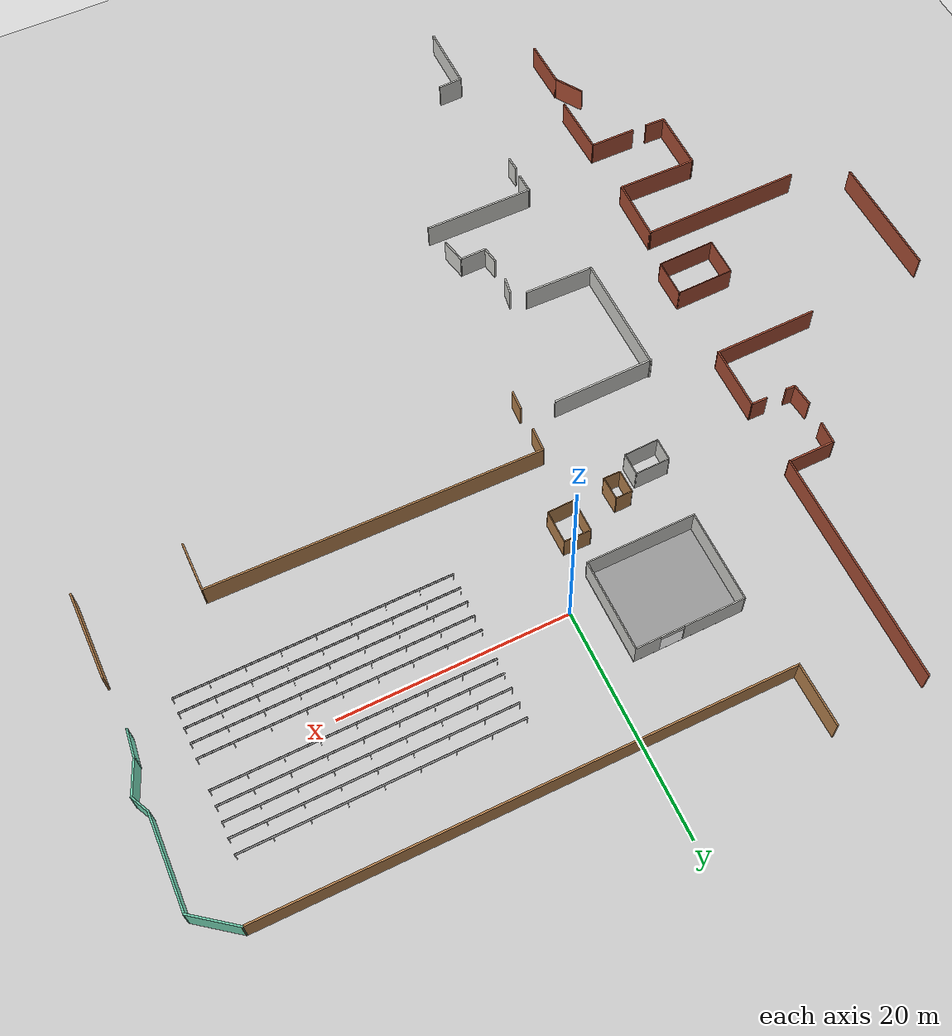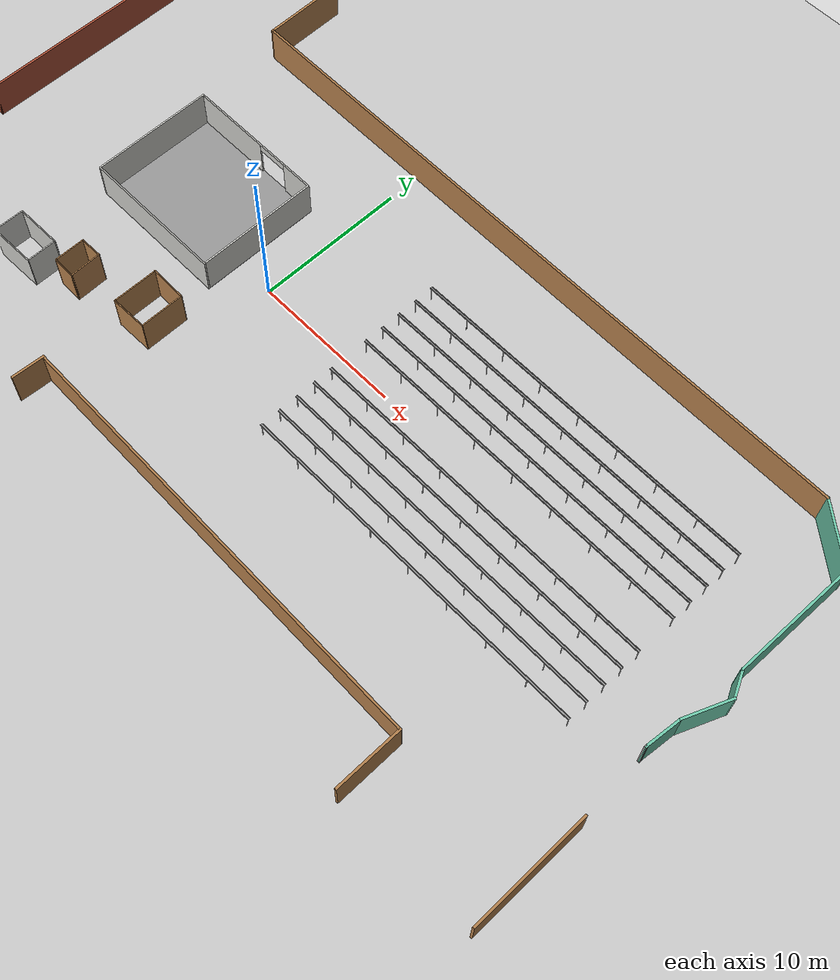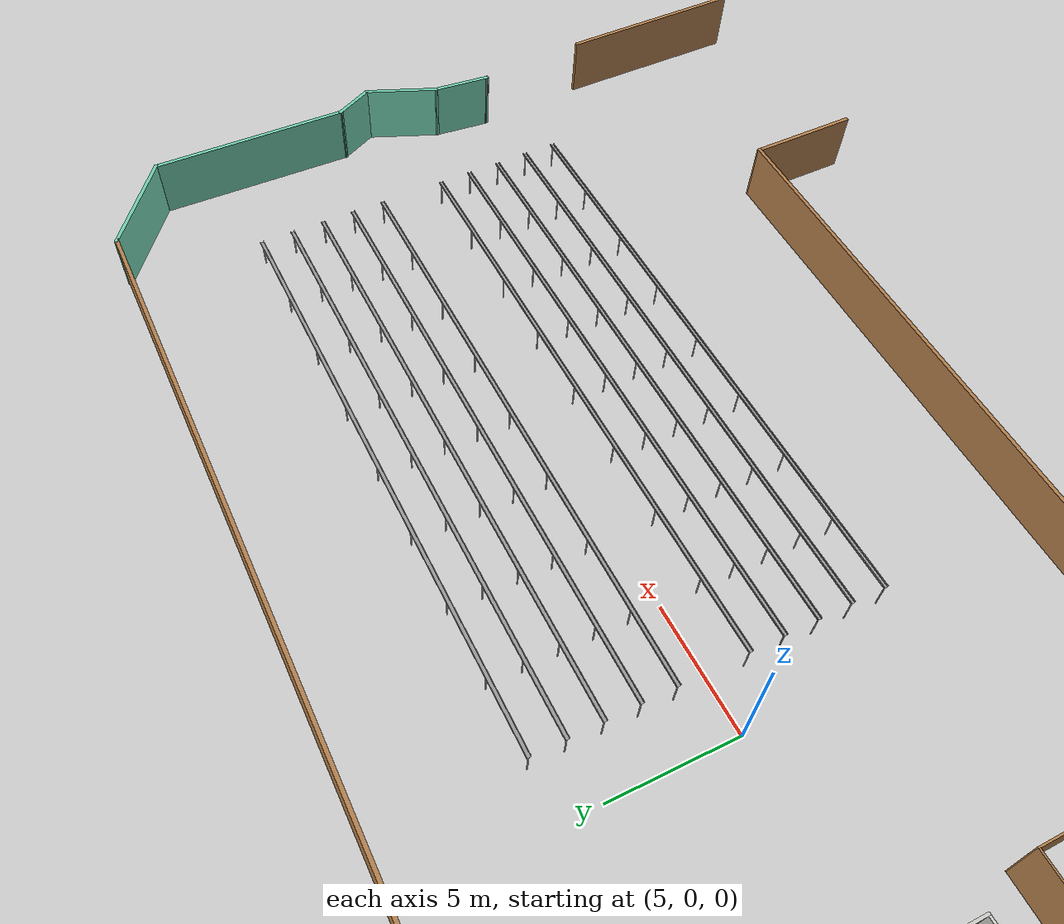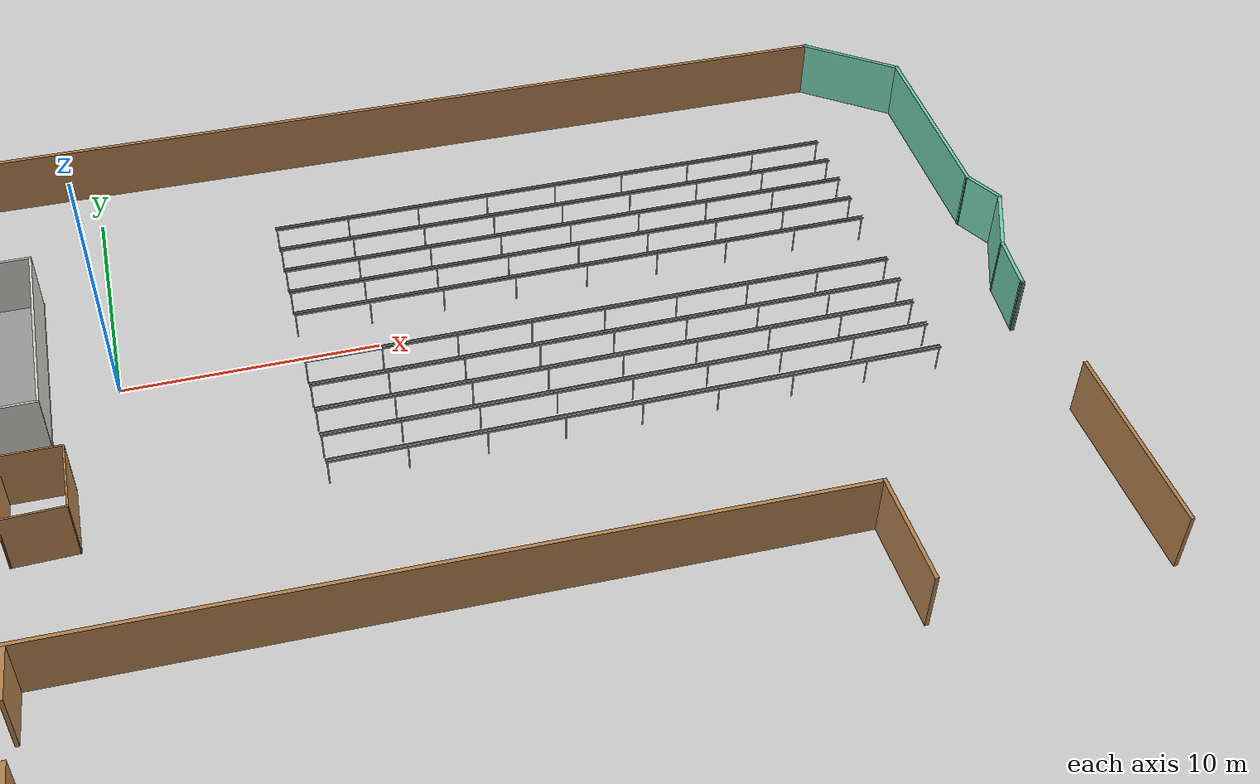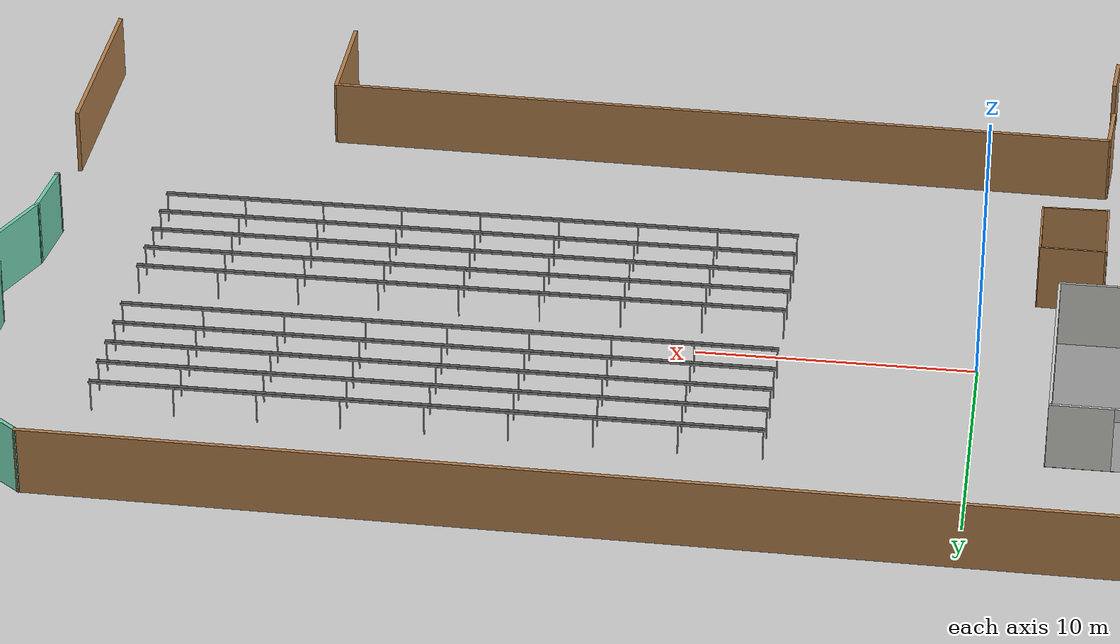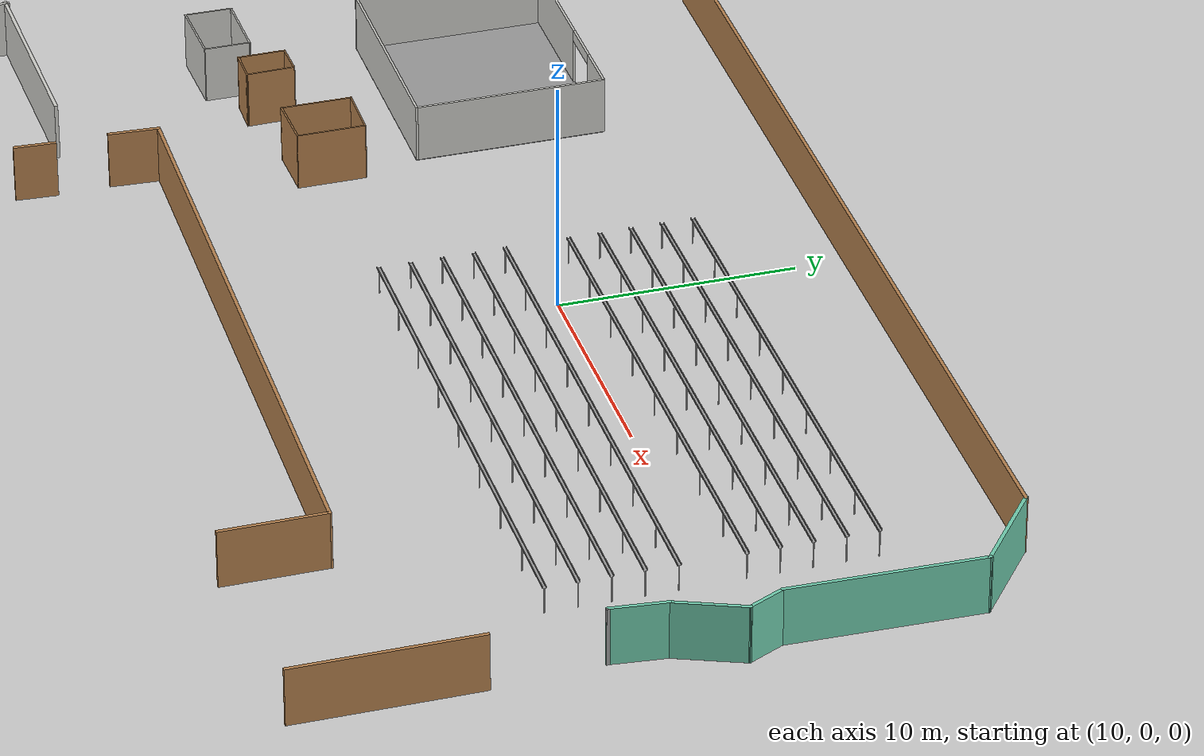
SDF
<?xml version="1.0" encoding="utf-8"?>
<sdf version="1.4">
	<world name="default">
		<physics type="ode">
			<real_time_update_rate>200</real_time_update_rate>
			<real_time_factor>1</real_time_factor>
			<max_step_size>0.005</max_step_size>
			<gravity>0 0 -9.8</gravity>
		</physics>
		<model name="pole_0">
			<static>1</static>
			<pose>7.000 -6.640 0.575 0.0 0.0 0.0</pose>
			<link name="link">
				<collision name="collision">
					<geometry>
						<cylinder>
							<length>1.15</length>
							<radius>0.025</radius>
						</cylinder>
					</geometry>
				</collision>
				<visual name="visual">
					<geometry>
						<cylinder>
							<length>1.15</length>
							<radius>0.025</radius>
						</cylinder>
					</geometry>
					<material>
						<script>
							<uri>file://media/materials/scripts/gazebo.material</uri>
							<name>Gazebo/Chrome</name>
						</script>
						<shader type="vertex">
							<normal_map>__default__</normal_map>
						</shader>
						<emissive>0.1 0.1 0.1 1</emissive>
						<specular>0.01 0.01 0.01 1</specular>
						<ambient>0.5 0.5 0.5 1</ambient>
						<diffuse>0.05 0.05 0.05 1</diffuse>
					</material>
				</visual>
			</link>
		</model>
		<model name="pole_1">
			<static>1</static>
			<pose>7.000 -5.320 0.575 0.0 0.0 0.0</pose>
			<link name="link">
				<collision name="collision">
					<geometry>
						<cylinder>
							<length>1.15</length>
							<radius>0.025</radius>
						</cylinder>
					</geometry>
				</collision>
				<visual name="visual">
					<geometry>
						<cylinder>
							<length>1.15</length>
							<radius>0.025</radius>
						</cylinder>
					</geometry>
					<material>
						<script>
							<uri>file://media/materials/scripts/gazebo.material</uri>
							<name>Gazebo/Chrome</name>
						</script>
						<shader type="vertex">
							<normal_map>__default__</normal_map>
						</shader>
						<emissive>0.1 0.1 0.1 1</emissive>
						<specular>0.01 0.01 0.01 1</specular>
						<ambient>0.5 0.5 0.5 1</ambient>
						<diffuse>0.05 0.05 0.05 1</diffuse>
					</material>
				</visual>
			</link>
		</model>
		<model name="pole_2">
			<static>1</static>
			<pose>7.000 -4.000 0.575 0.0 0.0 0.0</pose>
			<link name="link">
				<collision name="collision">
					<geometry>
						<cylinder>
							<length>1.15</length>
							<radius>0.025</radius>
						</cylinder>
					</geometry>
				</collision>
				<visual name="visual">
					<geometry>
						<cylinder>
							<length>1.15</length>
							<radius>0.025</radius>
						</cylinder>
					</geometry>
					<material>
						<script>
							<uri>file://media/materials/scripts/gazebo.material</uri>
							<name>Gazebo/Chrome</name>
						</script>
						<shader type="vertex">
							<normal_map>__default__</normal_map>
						</shader>
						<emissive>0.1 0.1 0.1 1</emissive>
						<specular>0.01 0.01 0.01 1</specular>
						<ambient>0.5 0.5 0.5 1</ambient>
						<diffuse>0.05 0.05 0.05 1</diffuse>
					</material>
				</visual>
			</link>
		</model>
		<model name="pole_3">
			<static>1</static>
			<pose>7.000 -2.680 0.575 0.0 0.0 0.0</pose>
			<link name="link">
				<collision name="collision">
					<geometry>
						<cylinder>
							<length>1.15</length>
							<radius>0.025</radius>
						</cylinder>
					</geometry>
				</collision>
				<visual name="visual">
					<geometry>
						<cylinder>
							<length>1.15</length>
							<radius>0.025</radius>
						</cylinder>
					</geometry>
					<material>
						<script>
							<uri>file://media/materials/scripts/gazebo.material</uri>
							<name>Gazebo/Chrome</name>
						</script>
						<shader type="vertex">
							<normal_map>__default__</normal_map>
						</shader>
						<emissive>0.1 0.1 0.1 1</emissive>
						<specular>0.01 0.01 0.01 1</specular>
						<ambient>0.5 0.5 0.5 1</ambient>
						<diffuse>0.05 0.05 0.05 1</diffuse>
					</material>
				</visual>
			</link>
		</model>
		<model name="pole_4">
			<static>1</static>
			<pose>7.000 -1.360 0.575 0.0 0.0 0.0</pose>
			<link name="link">
				<collision name="collision">
					<geometry>
						<cylinder>
							<length>1.15</length>
							<radius>0.025</radius>
						</cylinder>
					</geometry>
				</collision>
				<visual name="visual">
					<geometry>
						<cylinder>
							<length>1.15</length>
							<radius>0.025</radius>
						</cylinder>
					</geometry>
					<material>
						<script>
							<uri>file://media/materials/scripts/gazebo.material</uri>
							<name>Gazebo/Chrome</name>
						</script>
						<shader type="vertex">
							<normal_map>__default__</normal_map>
						</shader>
						<emissive>0.1 0.1 0.1 1</emissive>
						<specular>0.01 0.01 0.01 1</specular>
						<ambient>0.5 0.5 0.5 1</ambient>
						<diffuse>0.05 0.05 0.05 1</diffuse>
					</material>
				</visual>
			</link>
		</model>
		<model name="pole_5">
			<static>1</static>
			<pose>9.940 -6.640 0.575 0.0 0.0 0.0</pose>
			<link name="link">
				<collision name="collision">
					<geometry>
						<cylinder>
							<length>1.15</length>
							<radius>0.025</radius>
						</cylinder>
					</geometry>
				</collision>
				<visual name="visual">
					<geometry>
						<cylinder>
							<length>1.15</length>
							<radius>0.025</radius>
						</cylinder>
					</geometry>
					<material>
						<script>
							<uri>file://media/materials/scripts/gazebo.material</uri>
							<name>Gazebo/Chrome</name>
						</script>
						<shader type="vertex">
							<normal_map>__default__</normal_map>
						</shader>
						<emissive>0.1 0.1 0.1 1</emissive>
						<specular>0.01 0.01 0.01 1</specular>
						<ambient>0.5 0.5 0.5 1</ambient>
						<diffuse>0.05 0.05 0.05 1</diffuse>
					</material>
				</visual>
			</link>
		</model>
		<model name="pole_6">
			<static>1</static>
			<pose>9.940 -5.320 0.575 0.0 0.0 0.0</pose>
			<link name="link">
				<collision name="collision">
					<geometry>
						<cylinder>
							<length>1.15</length>
							<radius>0.025</radius>
						</cylinder>
					</geometry>
				</collision>
				<visual name="visual">
					<geometry>
						<cylinder>
							<length>1.15</length>
							<radius>0.025</radius>
						</cylinder>
					</geometry>
					<material>
						<script>
							<uri>file://media/materials/scripts/gazebo.material</uri>
							<name>Gazebo/Chrome</name>
						</script>
						<shader type="vertex">
							<normal_map>__default__</normal_map>
						</shader>
						<emissive>0.1 0.1 0.1 1</emissive>
						<specular>0.01 0.01 0.01 1</specular>
						<ambient>0.5 0.5 0.5 1</ambient>
						<diffuse>0.05 0.05 0.05 1</diffuse>
					</material>
				</visual>
			</link>
		</model>
		<model name="pole_7">
			<static>1</static>
			<pose>9.940 -4.000 0.575 0.0 0.0 0.0</pose>
			<link name="link">
				<collision name="collision">
					<geometry>
						<cylinder>
							<length>1.15</length>
							<radius>0.025</radius>
						</cylinder>
					</geometry>
				</collision>
				<visual name="visual">
					<geometry>
						<cylinder>
							<length>1.15</length>
							<radius>0.025</radius>
						</cylinder>
					</geometry>
					<material>
						<script>
							<uri>file://media/materials/scripts/gazebo.material</uri>
							<name>Gazebo/Chrome</name>
						</script>
						<shader type="vertex">
							<normal_map>__default__</normal_map>
						</shader>
						<emissive>0.1 0.1 0.1 1</emissive>
						<specular>0.01 0.01 0.01 1</specular>
						<ambient>0.5 0.5 0.5 1</ambient>
						<diffuse>0.05 0.05 0.05 1</diffuse>
					</material>
				</visual>
			</link>
		</model>
		<model name="pole_8">
			<static>1</static>
			<pose>9.940 -2.680 0.575 0.0 0.0 0.0</pose>
			<link name="link">
				<collision name="collision">
					<geometry>
						<cylinder>
							<length>1.15</length>
							<radius>0.025</radius>
						</cylinder>
					</geometry>
				</collision>
				<visual name="visual">
					<geometry>
						<cylinder>
							<length>1.15</length>
							<radius>0.025</radius>
						</cylinder>
					</geometry>
					<material>
						<script>
							<uri>file://media/materials/scripts/gazebo.material</uri>
							<name>Gazebo/Chrome</name>
						</script>
						<shader type="vertex">
							<normal_map>__default__</normal_map>
						</shader>
						<emissive>0.1 0.1 0.1 1</emissive>
						<specular>0.01 0.01 0.01 1</specular>
						<ambient>0.5 0.5 0.5 1</ambient>
						<diffuse>0.05 0.05 0.05 1</diffuse>
					</material>
				</visual>
			</link>
		</model>
		<model name="pole_9">
			<static>1</static>
			<pose>9.940 -1.360 0.575 0.0 0.0 0.0</pose>
			<link name="link">
				<collision name="collision">
					<geometry>
						<cylinder>
							<length>1.15</length>
							<radius>0.025</radius>
						</cylinder>
					</geometry>
				</collision>
				<visual name="visual">
					<geometry>
						<cylinder>
							<length>1.15</length>
							<radius>0.025</radius>
						</cylinder>
					</geometry>
					<material>
						<script>
							<uri>file://media/materials/scripts/gazebo.material</uri>
							<name>Gazebo/Chrome</name>
						</script>
						<shader type="vertex">
							<normal_map>__default__</normal_map>
						</shader>
						<emissive>0.1 0.1 0.1 1</emissive>
						<specular>0.01 0.01 0.01 1</specular>
						<ambient>0.5 0.5 0.5 1</ambient>
						<diffuse>0.05 0.05 0.05 1</diffuse>
					</material>
				</visual>
			</link>
		</model>
		<model name="pole_10">
			<static>1</static>
			<pose>12.880 -6.640 0.575 0.0 0.0 0.0</pose>
			<link name="link">
				<collision name="collision">
					<geometry>
						<cylinder>
							<length>1.15</length>
							<radius>0.025</radius>
						</cylinder>
					</geometry>
				</collision>
				<visual name="visual">
					<geometry>
						<cylinder>
							<length>1.15</length>
							<radius>0.025</radius>
						</cylinder>
					</geometry>
					<material>
						<script>
							<uri>file://media/materials/scripts/gazebo.material</uri>
							<name>Gazebo/Chrome</name>
						</script>
						<shader type="vertex">
							<normal_map>__default__</normal_map>
						</shader>
						<emissive>0.1 0.1 0.1 1</emissive>
						<specular>0.01 0.01 0.01 1</specular>
						<ambient>0.5 0.5 0.5 1</ambient>
						<diffuse>0.05 0.05 0.05 1</diffuse>
					</material>
				</visual>
			</link>
		</model>
		<model name="pole_11">
			<static>1</static>
			<pose>12.880 -5.320 0.575 0.0 0.0 0.0</pose>
			<link name="link">
				<collision name="collision">
					<geometry>
						<cylinder>
							<length>1.15</length>
							<radius>0.025</radius>
						</cylinder>
					</geometry>
				</collision>
				<visual name="visual">
					<geometry>
						<cylinder>
							<length>1.15</length>
							<radius>0.025</radius>
						</cylinder>
					</geometry>
					<material>
						<script>
							<uri>file://media/materials/scripts/gazebo.material</uri>
							<name>Gazebo/Chrome</name>
						</script>
						<shader type="vertex">
							<normal_map>__default__</normal_map>
						</shader>
						<emissive>0.1 0.1 0.1 1</emissive>
						<specular>0.01 0.01 0.01 1</specular>
						<ambient>0.5 0.5 0.5 1</ambient>
						<diffuse>0.05 0.05 0.05 1</diffuse>
					</material>
				</visual>
			</link>
		</model>
		<model name="pole_12">
			<static>1</static>
			<pose>12.880 -4.000 0.575 0.0 0.0 0.0</pose>
			<link name="link">
				<collision name="collision">
					<geometry>
						<cylinder>
							<length>1.15</length>
							<radius>0.025</radius>
						</cylinder>
					</geometry>
				</collision>
				<visual name="visual">
					<geometry>
						<cylinder>
							<length>1.15</length>
							<radius>0.025</radius>
						</cylinder>
					</geometry>
					<material>
						<script>
							<uri>file://media/materials/scripts/gazebo.material</uri>
							<name>Gazebo/Chrome</name>
						</script>
						<shader type="vertex">
							<normal_map>__default__</normal_map>
						</shader>
						<emissive>0.1 0.1 0.1 1</emissive>
						<specular>0.01 0.01 0.01 1</specular>
						<ambient>0.5 0.5 0.5 1</ambient>
						<diffuse>0.05 0.05 0.05 1</diffuse>
					</material>
				</visual>
			</link>
		</model>
		<model name="pole_13">
			<static>1</static>
			<pose>12.880 -2.680 0.575 0.0 0.0 0.0</pose>
			<link name="link">
				<collision name="collision">
					<geometry>
						<cylinder>
							<length>1.15</length>
							<radius>0.025</radius>
						</cylinder>
					</geometry>
				</collision>
				<visual name="visual">
					<geometry>
						<cylinder>
							<length>1.15</length>
							<radius>0.025</radius>
						</cylinder>
					</geometry>
					<material>
						<script>
							<uri>file://media/materials/scripts/gazebo.material</uri>
							<name>Gazebo/Chrome</name>
						</script>
						<shader type="vertex">
							<normal_map>__default__</normal_map>
						</shader>
						<emissive>0.1 0.1 0.1 1</emissive>
						<specular>0.01 0.01 0.01 1</specular>
						<ambient>0.5 0.5 0.5 1</ambient>
						<diffuse>0.05 0.05 0.05 1</diffuse>
					</material>
				</visual>
			</link>
		</model>
		<model name="pole_14">
			<static>1</static>
			<pose>12.880 -1.360 0.575 0.0 0.0 0.0</pose>
			<link name="link">
				<collision name="collision">
					<geometry>
						<cylinder>
							<length>1.15</length>
							<radius>0.025</radius>
						</cylinder>
					</geometry>
				</collision>
				<visual name="visual">
					<geometry>
						<cylinder>
							<length>1.15</length>
							<radius>0.025</radius>
						</cylinder>
					</geometry>
					<material>
						<script>
							<uri>file://media/materials/scripts/gazebo.material</uri>
							<name>Gazebo/Chrome</name>
						</script>
						<shader type="vertex">
							<normal_map>__default__</normal_map>
						</shader>
						<emissive>0.1 0.1 0.1 1</emissive>
						<specular>0.01 0.01 0.01 1</specular>
						<ambient>0.5 0.5 0.5 1</ambient>
						<diffuse>0.05 0.05 0.05 1</diffuse>
					</material>
				</visual>
			</link>
		</model>
		<model name="pole_15">
			<static>1</static>
			<pose>15.820 -6.640 0.575 0.0 0.0 0.0</pose>
			<link name="link">
				<collision name="collision">
					<geometry>
						<cylinder>
							<length>1.15</length>
							<radius>0.025</radius>
						</cylinder>
					</geometry>
				</collision>
				<visual name="visual">
					<geometry>
						<cylinder>
							<length>1.15</length>
							<radius>0.025</radius>
						</cylinder>
					</geometry>
					<material>
						<script>
							<uri>file://media/materials/scripts/gazebo.material</uri>
							<name>Gazebo/Chrome</name>
						</script>
						<shader type="vertex">
							<normal_map>__default__</normal_map>
						</shader>
						<emissive>0.1 0.1 0.1 1</emissive>
						<specular>0.01 0.01 0.01 1</specular>
						<ambient>0.5 0.5 0.5 1</ambient>
						<diffuse>0.05 0.05 0.05 1</diffuse>
					</material>
				</visual>
			</link>
		</model>
		<model name="pole_16">
			<static>1</static>
			<pose>15.820 -5.320 0.575 0.0 0.0 0.0</pose>
			<link name="link">
				<collision name="collision">
					<geometry>
						<cylinder>
							<length>1.15</length>
							<radius>0.025</radius>
						</cylinder>
					</geometry>
				</collision>
				<visual name="visual">
					<geometry>
						<cylinder>
							<length>1.15</length>
							<radius>0.025</radius>
						</cylinder>
					</geometry>
					<material>
						<script>
							<uri>file://media/materials/scripts/gazebo.material</uri>
							<name>Gazebo/Chrome</name>
						</script>
						<shader type="vertex">
							<normal_map>__default__</normal_map>
						</shader>
						<emissive>0.1 0.1 0.1 1</emissive>
						<specular>0.01 0.01 0.01 1</specular>
						<ambient>0.5 0.5 0.5 1</ambient>
						<diffuse>0.05 0.05 0.05 1</diffuse>
					</material>
				</visual>
			</link>
		</model>
		<model name="pole_17">
			<static>1</static>
			<pose>15.820 -4.000 0.575 0.0 0.0 0.0</pose>
			<link name="link">
				<collision name="collision">
					<geometry>
						<cylinder>
							<length>1.15</length>
							<radius>0.025</radius>
						</cylinder>
					</geometry>
				</collision>
				<visual name="visual">
					<geometry>
						<cylinder>
							<length>1.15</length>
							<radius>0.025</radius>
						</cylinder>
					</geometry>
					<material>
						<script>
							<uri>file://media/materials/scripts/gazebo.material</uri>
							<name>Gazebo/Chrome</name>
						</script>
						<shader type="vertex">
							<normal_map>__default__</normal_map>
						</shader>
						<emissive>0.1 0.1 0.1 1</emissive>
						<specular>0.01 0.01 0.01 1</specular>
						<ambient>0.5 0.5 0.5 1</ambient>
						<diffuse>0.05 0.05 0.05 1</diffuse>
					</material>
				</visual>
			</link>
		</model>
		<model name="pole_18">
			<static>1</static>
			<pose>15.820 -2.680 0.575 0.0 0.0 0.0</pose>
			<link name="link">
				<collision name="collision">
					<geometry>
						<cylinder>
							<length>1.15</length>
							<radius>0.025</radius>
						</cylinder>
					</geometry>
				</collision>
				<visual name="visual">
					<geometry>
						<cylinder>
							<length>1.15</length>
							<radius>0.025</radius>
						</cylinder>
					</geometry>
					<material>
						<script>
							<uri>file://media/materials/scripts/gazebo.material</uri>
							<name>Gazebo/Chrome</name>
						</script>
						<shader type="vertex">
							<normal_map>__default__</normal_map>
						</shader>
						<emissive>0.1 0.1 0.1 1</emissive>
						<specular>0.01 0.01 0.01 1</specular>
						<ambient>0.5 0.5 0.5 1</ambient>
						<diffuse>0.05 0.05 0.05 1</diffuse>
					</material>
				</visual>
			</link>
		</model>
		<model name="pole_19">
			<static>1</static>
			<pose>15.820 -1.360 0.575 0.0 0.0 0.0</pose>
			<link name="link">
				<collision name="collision">
					<geometry>
						<cylinder>
							<length>1.15</length>
							<radius>0.025</radius>
						</cylinder>
					</geometry>
				</collision>
				<visual name="visual">
					<geometry>
						<cylinder>
							<length>1.15</length>
							<radius>0.025</radius>
						</cylinder>
					</geometry>
					<material>
						<script>
							<uri>file://media/materials/scripts/gazebo.material</uri>
							<name>Gazebo/Chrome</name>
						</script>
						<shader type="vertex">
							<normal_map>__default__</normal_map>
						</shader>
						<emissive>0.1 0.1 0.1 1</emissive>
						<specular>0.01 0.01 0.01 1</specular>
						<ambient>0.5 0.5 0.5 1</ambient>
						<diffuse>0.05 0.05 0.05 1</diffuse>
					</material>
				</visual>
			</link>
		</model>
		<model name="pole_20">
			<static>1</static>
			<pose>18.760 -6.640 0.575 0.0 0.0 0.0</pose>
			<link name="link">
				<collision name="collision">
					<geometry>
						<cylinder>
							<length>1.15</length>
							<radius>0.025</radius>
						</cylinder>
					</geometry>
				</collision>
				<visual name="visual">
					<geometry>
						<cylinder>
							<length>1.15</length>
							<radius>0.025</radius>
						</cylinder>
					</geometry>
					<material>
						<script>
							<uri>file://media/materials/scripts/gazebo.material</uri>
							<name>Gazebo/Chrome</name>
						</script>
						<shader type="vertex">
							<normal_map>__default__</normal_map>
						</shader>
						<emissive>0.1 0.1 0.1 1</emissive>
						<specular>0.01 0.01 0.01 1</specular>
						<ambient>0.5 0.5 0.5 1</ambient>
						<diffuse>0.05 0.05 0.05 1</diffuse>
					</material>
				</visual>
			</link>
		</model>
		<model name="pole_21">
			<static>1</static>
			<pose>18.760 -5.320 0.575 0.0 0.0 0.0</pose>
			<link name="link">
				<collision name="collision">
					<geometry>
						<cylinder>
							<length>1.15</length>
							<radius>0.025</radius>
						</cylinder>
					</geometry>
				</collision>
				<visual name="visual">
					<geometry>
						<cylinder>
							<length>1.15</length>
							<radius>0.025</radius>
						</cylinder>
					</geometry>
					<material>
						<script>
							<uri>file://media/materials/scripts/gazebo.material</uri>
							<name>Gazebo/Chrome</name>
						</script>
						<shader type="vertex">
							<normal_map>__default__</normal_map>
						</shader>
						<emissive>0.1 0.1 0.1 1</emissive>
						<specular>0.01 0.01 0.01 1</specular>
						<ambient>0.5 0.5 0.5 1</ambient>
						<diffuse>0.05 0.05 0.05 1</diffuse>
					</material>
				</visual>
			</link>
		</model>
		<model name="pole_22">
			<static>1</static>
			<pose>18.760 -4.000 0.575 0.0 0.0 0.0</pose>
			<link name="link">
				<collision name="collision">
					<geometry>
						<cylinder>
							<length>1.15</length>
							<radius>0.025</radius>
						</cylinder>
					</geometry>
				</collision>
				<visual name="visual">
					<geometry>
						<cylinder>
							<length>1.15</length>
							<radius>0.025</radius>
						</cylinder>
					</geometry>
					<material>
						<script>
							<uri>file://media/materials/scripts/gazebo.material</uri>
							<name>Gazebo/Chrome</name>
						</script>
						<shader type="vertex">
							<normal_map>__default__</normal_map>
						</shader>
						<emissive>0.1 0.1 0.1 1</emissive>
						<specular>0.01 0.01 0.01 1</specular>
						<ambient>0.5 0.5 0.5 1</ambient>
						<diffuse>0.05 0.05 0.05 1</diffuse>
					</material>
				</visual>
			</link>
		</model>
		<model name="pole_23">
			<static>1</static>
			<pose>18.760 -2.680 0.575 0.0 0.0 0.0</pose>
			<link name="link">
				<collision name="collision">
					<geometry>
						<cylinder>
							<length>1.15</length>
							<radius>0.025</radius>
						</cylinder>
					</geometry>
				</collision>
				<visual name="visual">
					<geometry>
						<cylinder>
							<length>1.15</length>
							<radius>0.025</radius>
						</cylinder>
					</geometry>
					<material>
						<script>
							<uri>file://media/materials/scripts/gazebo.material</uri>
							<name>Gazebo/Chrome</name>
						</script>
						<shader type="vertex">
							<normal_map>__default__</normal_map>
						</shader>
						<emissive>0.1 0.1 0.1 1</emissive>
						<specular>0.01 0.01 0.01 1</specular>
						<ambient>0.5 0.5 0.5 1</ambient>
						<diffuse>0.05 0.05 0.05 1</diffuse>
					</material>
				</visual>
			</link>
		</model>
		<model name="pole_24">
			<static>1</static>
			<pose>18.760 -1.360 0.575 0.0 0.0 0.0</pose>
			<link name="link">
				<collision name="collision">
					<geometry>
						<cylinder>
							<length>1.15</length>
							<radius>0.025</radius>
						</cylinder>
					</geometry>
				</collision>
				<visual name="visual">
					<geometry>
						<cylinder>
							<length>1.15</length>
							<radius>0.025</radius>
						</cylinder>
					</geometry>
					<material>
						<script>
							<uri>file://media/materials/scripts/gazebo.material</uri>
							<name>Gazebo/Chrome</name>
						</script>
						<shader type="vertex">
							<normal_map>__default__</normal_map>
						</shader>
						<emissive>0.1 0.1 0.1 1</emissive>
						<specular>0.01 0.01 0.01 1</specular>
						<ambient>0.5 0.5 0.5 1</ambient>
						<diffuse>0.05 0.05 0.05 1</diffuse>
					</material>
				</visual>
			</link>
		</model>
		<model name="pole_25">
			<static>1</static>
			<pose>21.700 -6.640 0.575 0.0 0.0 0.0</pose>
			<link name="link">
				<collision name="collision">
					<geometry>
						<cylinder>
							<length>1.15</length>
							<radius>0.025</radius>
						</cylinder>
					</geometry>
				</collision>
				<visual name="visual">
					<geometry>
						<cylinder>
							<length>1.15</length>
							<radius>0.025</radius>
						</cylinder>
					</geometry>
					<material>
						<script>
							<uri>file://media/materials/scripts/gazebo.material</uri>
							<name>Gazebo/Chrome</name>
						</script>
						<shader type="vertex">
							<normal_map>__default__</normal_map>
						</shader>
						<emissive>0.1 0.1 0.1 1</emissive>
						<specular>0.01 0.01 0.01 1</specular>
						<ambient>0.5 0.5 0.5 1</ambient>
						<diffuse>0.05 0.05 0.05 1</diffuse>
					</material>
				</visual>
			</link>
		</model>
		<model name="pole_26">
			<static>1</static>
			<pose>21.700 -5.320 0.575 0.0 0.0 0.0</pose>
			<link name="link">
				<collision name="collision">
					<geometry>
						<cylinder>
							<length>1.15</length>
							<radius>0.025</radius>
						</cylinder>
					</geometry>
				</collision>
				<visual name="visual">
					<geometry>
						<cylinder>
							<length>1.15</length>
							<radius>0.025</radius>
						</cylinder>
					</geometry>
					<material>
						<script>
							<uri>file://media/materials/scripts/gazebo.material</uri>
							<name>Gazebo/Chrome</name>
						</script>
						<shader type="vertex">
							<normal_map>__default__</normal_map>
						</shader>
						<emissive>0.1 0.1 0.1 1</emissive>
						<specular>0.01 0.01 0.01 1</specular>
						<ambient>0.5 0.5 0.5 1</ambient>
						<diffuse>0.05 0.05 0.05 1</diffuse>
					</material>
				</visual>
			</link>
		</model>
		<model name="pole_27">
			<static>1</static>
			<pose>21.700 -4.000 0.575 0.0 0.0 0.0</pose>
			<link name="link">
				<collision name="collision">
					<geometry>
						<cylinder>
							<length>1.15</length>
							<radius>0.025</radius>
						</cylinder>
					</geometry>
				</collision>
				<visual name="visual">
					<geometry>
						<cylinder>
							<length>1.15</length>
							<radius>0.025</radius>
						</cylinder>
					</geometry>
					<material>
						<script>
							<uri>file://media/materials/scripts/gazebo.material</uri>
							<name>Gazebo/Chrome</name>
						</script>
						<shader type="vertex">
							<normal_map>__default__</normal_map>
						</shader>
						<emissive>0.1 0.1 0.1 1</emissive>
						<specular>0.01 0.01 0.01 1</specular>
						<ambient>0.5 0.5 0.5 1</ambient>
						<diffuse>0.05 0.05 0.05 1</diffuse>
					</material>
				</visual>
			</link>
		</model>
		<model name="pole_28">
			<static>1</static>
			<pose>21.700 -2.680 0.575 0.0 0.0 0.0</pose>
			<link name="link">
				<collision name="collision">
					<geometry>
						<cylinder>
							<length>1.15</length>
							<radius>0.025</radius>
						</cylinder>
					</geometry>
				</collision>
				<visual name="visual">
					<geometry>
						<cylinder>
							<length>1.15</length>
							<radius>0.025</radius>
						</cylinder>
					</geometry>
					<material>
						<script>
							<uri>file://media/materials/scripts/gazebo.material</uri>
							<name>Gazebo/Chrome</name>
						</script>
						<shader type="vertex">
							<normal_map>__default__</normal_map>
						</shader>
						<emissive>0.1 0.1 0.1 1</emissive>
						<specular>0.01 0.01 0.01 1</specular>
						<ambient>0.5 0.5 0.5 1</ambient>
						<diffuse>0.05 0.05 0.05 1</diffuse>
					</material>
				</visual>
			</link>
		</model>
		<model name="pole_29">
			<static>1</static>
			<pose>21.700 -1.360 0.575 0.0 0.0 0.0</pose>
			<link name="link">
				<collision name="collision">
					<geometry>
						<cylinder>
							<length>1.15</length>
							<radius>0.025</radius>
						</cylinder>
					</geometry>
				</collision>
				<visual name="visual">
					<geometry>
						<cylinder>
							<length>1.15</length>
							<radius>0.025</radius>
						</cylinder>
					</geometry>
					<material>
						<script>
							<uri>file://media/materials/scripts/gazebo.material</uri>
							<name>Gazebo/Chrome</name>
						</script>
						<shader type="vertex">
							<normal_map>__default__</normal_map>
						</shader>
						<emissive>0.1 0.1 0.1 1</emissive>
						<specular>0.01 0.01 0.01 1</specular>
						<ambient>0.5 0.5 0.5 1</ambient>
						<diffuse>0.05 0.05 0.05 1</diffuse>
					</material>
				</visual>
			</link>
		</model>
		<model name="pole_30">
			<static>1</static>
			<pose>24.640 -6.640 0.575 0.0 0.0 0.0</pose>
			<link name="link">
				<collision name="collision">
					<geometry>
						<cylinder>
							<length>1.15</length>
							<radius>0.025</radius>
						</cylinder>
					</geometry>
				</collision>
				<visual name="visual">
					<geometry>
						<cylinder>
							<length>1.15</length>
							<radius>0.025</radius>
						</cylinder>
					</geometry>
					<material>
						<script>
							<uri>file://media/materials/scripts/gazebo.material</uri>
							<name>Gazebo/Chrome</name>
						</script>
						<shader type="vertex">
							<normal_map>__default__</normal_map>
						</shader>
						<emissive>0.1 0.1 0.1 1</emissive>
						<specular>0.01 0.01 0.01 1</specular>
						<ambient>0.5 0.5 0.5 1</ambient>
						<diffuse>0.05 0.05 0.05 1</diffuse>
					</material>
				</visual>
			</link>
		</model>
		<model name="pole_31">
			<static>1</static>
			<pose>24.640 -5.320 0.575 0.0 0.0 0.0</pose>
			<link name="link">
				<collision name="collision">
					<geometry>
						<cylinder>
							<length>1.15</length>
							<radius>0.025</radius>
						</cylinder>
					</geometry>
				</collision>
				<visual name="visual">
					<geometry>
						<cylinder>
							<length>1.15</length>
							<radius>0.025</radius>
						</cylinder>
					</geometry>
					<material>
						<script>
							<uri>file://media/materials/scripts/gazebo.material</uri>
							<name>Gazebo/Chrome</name>
						</script>
						<shader type="vertex">
							<normal_map>__default__</normal_map>
						</shader>
						<emissive>0.1 0.1 0.1 1</emissive>
						<specular>0.01 0.01 0.01 1</specular>
						<ambient>0.5 0.5 0.5 1</ambient>
						<diffuse>0.05 0.05 0.05 1</diffuse>
					</material>
				</visual>
			</link>
		</model>
		<model name="pole_32">
			<static>1</static>
			<pose>24.640 -4.000 0.575 0.0 0.0 0.0</pose>
			<link name="link">
				<collision name="collision">
					<geometry>
						<cylinder>
							<length>1.15</length>
							<radius>0.025</radius>
						</cylinder>
					</geometry>
				</collision>
				<visual name="visual">
					<geometry>
						<cylinder>
							<length>1.15</length>
							<radius>0.025</radius>
						</cylinder>
					</geometry>
					<material>
						<script>
							<uri>file://media/materials/scripts/gazebo.material</uri>
							<name>Gazebo/Chrome</name>
						</script>
						<shader type="vertex">
							<normal_map>__default__</normal_map>
						</shader>
						<emissive>0.1 0.1 0.1 1</emissive>
						<specular>0.01 0.01 0.01 1</specular>
						<ambient>0.5 0.5 0.5 1</ambient>
						<diffuse>0.05 0.05 0.05 1</diffuse>
					</material>
				</visual>
			</link>
		</model>
		<model name="pole_33">
			<static>1</static>
			<pose>24.640 -2.680 0.575 0.0 0.0 0.0</pose>
			<link name="link">
				<collision name="collision">
					<geometry>
						<cylinder>
							<length>1.15</length>
							<radius>0.025</radius>
						</cylinder>
					</geometry>
				</collision>
				<visual name="visual">
					<geometry>
						<cylinder>
							<length>1.15</length>
							<radius>0.025</radius>
						</cylinder>
					</geometry>
					<material>
						<script>
							<uri>file://media/materials/scripts/gazebo.material</uri>
							<name>Gazebo/Chrome</name>
						</script>
						<shader type="vertex">
							<normal_map>__default__</normal_map>
						</shader>
						<emissive>0.1 0.1 0.1 1</emissive>
						<specular>0.01 0.01 0.01 1</specular>
						<ambient>0.5 0.5 0.5 1</ambient>
						<diffuse>0.05 0.05 0.05 1</diffuse>
					</material>
				</visual>
			</link>
		</model>
		<model name="pole_34">
			<static>1</static>
			<pose>24.640 -1.360 0.575 0.0 0.0 0.0</pose>
			<link name="link">
				<collision name="collision">
					<geometry>
						<cylinder>
							<length>1.15</length>
							<radius>0.025</radius>
						</cylinder>
					</geometry>
				</collision>
				<visual name="visual">
					<geometry>
						<cylinder>
							<length>1.15</length>
							<radius>0.025</radius>
						</cylinder>
					</geometry>
					<material>
						<script>
							<uri>file://media/materials/scripts/gazebo.material</uri>
							<name>Gazebo/Chrome</name>
						</script>
						<shader type="vertex">
							<normal_map>__default__</normal_map>
						</shader>
						<emissive>0.1 0.1 0.1 1</emissive>
						<specular>0.01 0.01 0.01 1</specular>
						<ambient>0.5 0.5 0.5 1</ambient>
						<diffuse>0.05 0.05 0.05 1</diffuse>
					</material>
				</visual>
			</link>
		</model>
		<model name="pole_35">
			<static>1</static>
			<pose>27.580 -6.640 0.575 0.0 0.0 0.0</pose>
			<link name="link">
				<collision name="collision">
					<geometry>
						<cylinder>
							<length>1.15</length>
							<radius>0.025</radius>
						</cylinder>
					</geometry>
				</collision>
				<visual name="visual">
					<geometry>
						<cylinder>
							<length>1.15</length>
							<radius>0.025</radius>
						</cylinder>
					</geometry>
					<material>
						<script>
							<uri>file://media/materials/scripts/gazebo.material</uri>
							<name>Gazebo/Chrome</name>
						</script>
						<shader type="vertex">
							<normal_map>__default__</normal_map>
						</shader>
						<emissive>0.1 0.1 0.1 1</emissive>
						<specular>0.01 0.01 0.01 1</specular>
						<ambient>0.5 0.5 0.5 1</ambient>
						<diffuse>0.05 0.05 0.05 1</diffuse>
					</material>
				</visual>
			</link>
		</model>
		<model name="pole_36">
			<static>1</static>
			<pose>27.580 -5.320 0.575 0.0 0.0 0.0</pose>
			<link name="link">
				<collision name="collision">
					<geometry>
						<cylinder>
							<length>1.15</length>
							<radius>0.025</radius>
						</cylinder>
					</geometry>
				</collision>
				<visual name="visual">
					<geometry>
						<cylinder>
							<length>1.15</length>
							<radius>0.025</radius>
						</cylinder>
					</geometry>
					<material>
						<script>
							<uri>file://media/materials/scripts/gazebo.material</uri>
							<name>Gazebo/Chrome</name>
						</script>
						<shader type="vertex">
							<normal_map>__default__</normal_map>
						</shader>
						<emissive>0.1 0.1 0.1 1</emissive>
						<specular>0.01 0.01 0.01 1</specular>
						<ambient>0.5 0.5 0.5 1</ambient>
						<diffuse>0.05 0.05 0.05 1</diffuse>
					</material>
				</visual>
			</link>
		</model>
		<model name="pole_37">
			<static>1</static>
			<pose>27.580 -4.000 0.575 0.0 0.0 0.0</pose>
			<link name="link">
				<collision name="collision">
					<geometry>
						<cylinder>
							<length>1.15</length>
							<radius>0.025</radius>
						</cylinder>
					</geometry>
				</collision>
				<visual name="visual">
					<geometry>
						<cylinder>
							<length>1.15</length>
							<radius>0.025</radius>
						</cylinder>
					</geometry>
					<material>
						<script>
							<uri>file://media/materials/scripts/gazebo.material</uri>
							<name>Gazebo/Chrome</name>
						</script>
						<shader type="vertex">
							<normal_map>__default__</normal_map>
						</shader>
						<emissive>0.1 0.1 0.1 1</emissive>
						<specular>0.01 0.01 0.01 1</specular>
						<ambient>0.5 0.5 0.5 1</ambient>
						<diffuse>0.05 0.05 0.05 1</diffuse>
					</material>
				</visual>
			</link>
		</model>
		<model name="pole_38">
			<static>1</static>
			<pose>27.580 -2.680 0.575 0.0 0.0 0.0</pose>
			<link name="link">
				<collision name="collision">
					<geometry>
						<cylinder>
							<length>1.15</length>
							<radius>0.025</radius>
						</cylinder>
					</geometry>
				</collision>
				<visual name="visual">
					<geometry>
						<cylinder>
							<length>1.15</length>
							<radius>0.025</radius>
						</cylinder>
					</geometry>
					<material>
						<script>
							<uri>file://media/materials/scripts/gazebo.material</uri>
							<name>Gazebo/Chrome</name>
						</script>
						<shader type="vertex">
							<normal_map>__default__</normal_map>
						</shader>
						<emissive>0.1 0.1 0.1 1</emissive>
						<specular>0.01 0.01 0.01 1</specular>
						<ambient>0.5 0.5 0.5 1</ambient>
						<diffuse>0.05 0.05 0.05 1</diffuse>
					</material>
				</visual>
			</link>
		</model>
		<model name="pole_39">
			<static>1</static>
			<pose>27.580 -1.360 0.575 0.0 0.0 0.0</pose>
			<link name="link">
				<collision name="collision">
					<geometry>
						<cylinder>
							<length>1.15</length>
							<radius>0.025</radius>
						</cylinder>
					</geometry>
				</collision>
				<visual name="visual">
					<geometry>
						<cylinder>
							<length>1.15</length>
							<radius>0.025</radius>
						</cylinder>
					</geometry>
					<material>
						<script>
							<uri>file://media/materials/scripts/gazebo.material</uri>
							<name>Gazebo/Chrome</name>
						</script>
						<shader type="vertex">
							<normal_map>__default__</normal_map>
						</shader>
						<emissive>0.1 0.1 0.1 1</emissive>
						<specular>0.01 0.01 0.01 1</specular>
						<ambient>0.5 0.5 0.5 1</ambient>
						<diffuse>0.05 0.05 0.05 1</diffuse>
					</material>
				</visual>
			</link>
		</model>
		<model name="pole_40">
			<static>1</static>
			<pose>30.520 -6.640 0.575 0.0 0.0 0.0</pose>
			<link name="link">
				<collision name="collision">
					<geometry>
						<cylinder>
							<length>1.15</length>
							<radius>0.025</radius>
						</cylinder>
					</geometry>
				</collision>
				<visual name="visual">
					<geometry>
						<cylinder>
							<length>1.15</length>
							<radius>0.025</radius>
						</cylinder>
					</geometry>
					<material>
						<script>
							<uri>file://media/materials/scripts/gazebo.material</uri>
							<name>Gazebo/Chrome</name>
						</script>
						<shader type="vertex">
							<normal_map>__default__</normal_map>
						</shader>
						<emissive>0.1 0.1 0.1 1</emissive>
						<specular>0.01 0.01 0.01 1</specular>
						<ambient>0.5 0.5 0.5 1</ambient>
						<diffuse>0.05 0.05 0.05 1</diffuse>
					</material>
				</visual>
			</link>
		</model>
		<model name="pole_41">
			<static>1</static>
			<pose>30.520 -5.320 0.575 0.0 0.0 0.0</pose>
			<link name="link">
				<collision name="collision">
					<geometry>
						<cylinder>
							<length>1.15</length>
							<radius>0.025</radius>
						</cylinder>
					</geometry>
				</collision>
				<visual name="visual">
					<geometry>
						<cylinder>
							<length>1.15</length>
							<radius>0.025</radius>
						</cylinder>
					</geometry>
					<material>
						<script>
							<uri>file://media/materials/scripts/gazebo.material</uri>
							<name>Gazebo/Chrome</name>
						</script>
						<shader type="vertex">
							<normal_map>__default__</normal_map>
						</shader>
						<emissive>0.1 0.1 0.1 1</emissive>
						<specular>0.01 0.01 0.01 1</specular>
						<ambient>0.5 0.5 0.5 1</ambient>
						<diffuse>0.05 0.05 0.05 1</diffuse>
					</material>
				</visual>
			</link>
		</model>
		<model name="pole_42">
			<static>1</static>
			<pose>30.520 -4.000 0.575 0.0 0.0 0.0</pose>
			<link name="link">
				<collision name="collision">
					<geometry>
						<cylinder>
							<length>1.15</length>
							<radius>0.025</radius>
						</cylinder>
					</geometry>
				</collision>
				<visual name="visual">
					<geometry>
						<cylinder>
							<length>1.15</length>
							<radius>0.025</radius>
						</cylinder>
					</geometry>
					<material>
						<script>
							<uri>file://media/materials/scripts/gazebo.material</uri>
							<name>Gazebo/Chrome</name>
						</script>
						<shader type="vertex">
							<normal_map>__default__</normal_map>
						</shader>
						<emissive>0.1 0.1 0.1 1</emissive>
						<specular>0.01 0.01 0.01 1</specular>
						<ambient>0.5 0.5 0.5 1</ambient>
						<diffuse>0.05 0.05 0.05 1</diffuse>
					</material>
				</visual>
			</link>
		</model>
		<model name="pole_43">
			<static>1</static>
			<pose>30.520 -2.680 0.575 0.0 0.0 0.0</pose>
			<link name="link">
				<collision name="collision">
					<geometry>
						<cylinder>
							<length>1.15</length>
							<radius>0.025</radius>
						</cylinder>
					</geometry>
				</collision>
				<visual name="visual">
					<geometry>
						<cylinder>
							<length>1.15</length>
							<radius>0.025</radius>
						</cylinder>
					</geometry>
					<material>
						<script>
							<uri>file://media/materials/scripts/gazebo.material</uri>
							<name>Gazebo/Chrome</name>
						</script>
						<shader type="vertex">
							<normal_map>__default__</normal_map>
						</shader>
						<emissive>0.1 0.1 0.1 1</emissive>
						<specular>0.01 0.01 0.01 1</specular>
						<ambient>0.5 0.5 0.5 1</ambient>
						<diffuse>0.05 0.05 0.05 1</diffuse>
					</material>
				</visual>
			</link>
		</model>
		<model name="pole_44">
			<static>1</static>
			<pose>30.520 -1.360 0.575 0.0 0.0 0.0</pose>
			<link name="link">
				<collision name="collision">
					<geometry>
						<cylinder>
							<length>1.15</length>
							<radius>0.025</radius>
						</cylinder>
					</geometry>
				</collision>
				<visual name="visual">
					<geometry>
						<cylinder>
							<length>1.15</length>
							<radius>0.025</radius>
						</cylinder>
					</geometry>
					<material>
						<script>
							<uri>file://media/materials/scripts/gazebo.material</uri>
							<name>Gazebo/Chrome</name>
						</script>
						<shader type="vertex">
							<normal_map>__default__</normal_map>
						</shader>
						<emissive>0.1 0.1 0.1 1</emissive>
						<specular>0.01 0.01 0.01 1</specular>
						<ambient>0.5 0.5 0.5 1</ambient>
						<diffuse>0.05 0.05 0.05 1</diffuse>
					</material>
				</visual>
			</link>
		</model>
		<model name="tray_0">
			<allow_auto_disable>1</allow_auto_disable>
			<static>1</static>
			<link name="link_0">
				<collision name="collision">
					<geometry>
						<box>
							<size>23.620 0.15 0.005</size>
						</box>
					</geometry>
				</collision>
				<visual name="visual">
					<geometry>
						<box>
							<size>23.620 0.15 0.005</size>
						</box>
					</geometry>
					<material>
						<script>
							<uri>file://media/materials/scripts/gazebo.material</uri>
							<name>Gazebo/Grey</name>
						</script>
						<emissive>0 0 0 1</emissive>
						<shader type="vertex">
							<normal_map>__default__</normal_map>
						</shader>
						<specular>0.01 0.01 0.01 1</specular>
						<lighting>1</lighting>
						<ambient>0.7 0.7 0.7 1</ambient>
						<diffuse>0.3 0.3 0.3 1</diffuse>
					</material>
					<cast_shadows>1</cast_shadows>
				</visual>
				<pose frame="">18.760 -6.640 1.14965 0.0 0.0 0.0</pose>
			</link>
		</model>
		<model name="tray_1">
			<allow_auto_disable>1</allow_auto_disable>
			<static>1</static>
			<link name="link_0">
				<collision name="collision">
					<geometry>
						<box>
							<size>23.620 0.15 0.005</size>
						</box>
					</geometry>
				</collision>
				<visual name="visual">
					<geometry>
						<box>
							<size>23.620 0.15 0.005</size>
						</box>
					</geometry>
					<material>
						<script>
							<uri>file://media/materials/scripts/gazebo.material</uri>
							<name>Gazebo/Grey</name>
						</script>
						<emissive>0 0 0 1</emissive>
						<shader type="vertex">
							<normal_map>__default__</normal_map>
						</shader>
						<specular>0.01 0.01 0.01 1</specular>
						<lighting>1</lighting>
						<ambient>0.7 0.7 0.7 1</ambient>
						<diffuse>0.3 0.3 0.3 1</diffuse>
					</material>
					<cast_shadows>1</cast_shadows>
				</visual>
				<pose frame="">18.760 -5.320 1.14965 0.0 0.0 0.0</pose>
			</link>
		</model>
		<model name="tray_2">
			<allow_auto_disable>1</allow_auto_disable>
			<static>1</static>
			<link name="link_0">
				<collision name="collision">
					<geometry>
						<box>
							<size>23.620 0.15 0.005</size>
						</box>
					</geometry>
				</collision>
				<visual name="visual">
					<geometry>
						<box>
							<size>23.620 0.15 0.005</size>
						</box>
					</geometry>
					<material>
						<script>
							<uri>file://media/materials/scripts/gazebo.material</uri>
							<name>Gazebo/Grey</name>
						</script>
						<emissive>0 0 0 1</emissive>
						<shader type="vertex">
							<normal_map>__default__</normal_map>
						</shader>
						<specular>0.01 0.01 0.01 1</specular>
						<lighting>1</lighting>
						<ambient>0.7 0.7 0.7 1</ambient>
						<diffuse>0.3 0.3 0.3 1</diffuse>
					</material>
					<cast_shadows>1</cast_shadows>
				</visual>
				<pose frame="">18.760 -4.000 1.14965 0.0 0.0 0.0</pose>
			</link>
		</model>
		<model name="tray_3">
			<allow_auto_disable>1</allow_auto_disable>
			<static>1</static>
			<link name="link_0">
				<collision name="collision">
					<geometry>
						<box>
							<size>23.620 0.15 0.005</size>
						</box>
					</geometry>
				</collision>
				<visual name="visual">
					<geometry>
						<box>
							<size>23.620 0.15 0.005</size>
						</box>
					</geometry>
					<material>
						<script>
							<uri>file://media/materials/scripts/gazebo.material</uri>
							<name>Gazebo/Grey</name>
						</script>
						<emissive>0 0 0 1</emissive>
						<shader type="vertex">
							<normal_map>__default__</normal_map>
						</shader>
						<specular>0.01 0.01 0.01 1</specular>
						<lighting>1</lighting>
						<ambient>0.7 0.7 0.7 1</ambient>
						<diffuse>0.3 0.3 0.3 1</diffuse>
					</material>
					<cast_shadows>1</cast_shadows>
				</visual>
				<pose frame="">18.760 -2.680 1.14965 0.0 0.0 0.0</pose>
			</link>
		</model>
		<model name="tray_4">
			<allow_auto_disable>1</allow_auto_disable>
			<static>1</static>
			<link name="link_0">
				<collision name="collision">
					<geometry>
						<box>
							<size>23.620 0.15 0.005</size>
						</box>
					</geometry>
				</collision>
				<visual name="visual">
					<geometry>
						<box>
							<size>23.620 0.15 0.005</size>
						</box>
					</geometry>
					<material>
						<script>
							<uri>file://media/materials/scripts/gazebo.material</uri>
							<name>Gazebo/Grey</name>
						</script>
						<emissive>0 0 0 1</emissive>
						<shader type="vertex">
							<normal_map>__default__</normal_map>
						</shader>
						<specular>0.01 0.01 0.01 1</specular>
						<lighting>1</lighting>
						<ambient>0.7 0.7 0.7 1</ambient>
						<diffuse>0.3 0.3 0.3 1</diffuse>
					</material>
					<cast_shadows>1</cast_shadows>
				</visual>
				<pose frame="">18.760 -1.360 1.14965 0.0 0.0 0.0</pose>
			</link>
		</model>
		<model name="tray_p2_0">
			<allow_auto_disable>1</allow_auto_disable>
			<static>1</static>
			<link name="link_0">
				<collision name="collision">
					<geometry>
						<box>
							<size>23.62 0.085 0.005</size>
						</box>
					</geometry>
				</collision>
				<visual name="visual">
					<geometry>
						<box>
							<size>23.62 0.085 0.005</size>
						</box>
					</geometry>
					<material>
						<script>
							<uri>file://media/materials/scripts/gazebo.material</uri>
							<name>Gazebo/Grey</name>
						</script>
						<emissive>0 0 0 1</emissive>
						<shader type="vertex">
							<normal_map>__default__</normal_map>
						</shader>
						<specular>0.01 0.01 0.01 1</specular>
						<lighting>1</lighting>
						<ambient>0.7 0.7 0.7 1</ambient>
						<diffuse>0.3 0.3 0.3 1</diffuse>
					</material>
					<cast_shadows>1</cast_shadows>
				</visual>
				<pose frame="">18.760 -6.715 1.19165 1.5707 0.0 0.0</pose>
			</link>
		</model>
		<model name="tray_p2_1">
			<allow_auto_disable>1</allow_auto_disable>
			<static>1</static>
			<link name="link_0">
				<collision name="collision">
					<geometry>
						<box>
							<size>23.62 0.085 0.005</size>
						</box>
					</geometry>
				</collision>
				<visual name="visual">
					<geometry>
						<box>
							<size>23.62 0.085 0.005</size>
						</box>
					</geometry>
					<material>
						<script>
							<uri>file://media/materials/scripts/gazebo.material</uri>
							<name>Gazebo/Grey</name>
						</script>
						<emissive>0 0 0 1</emissive>
						<shader type="vertex">
							<normal_map>__default__</normal_map>
						</shader>
						<specular>0.01 0.01 0.01 1</specular>
						<lighting>1</lighting>
						<ambient>0.7 0.7 0.7 1</ambient>
						<diffuse>0.3 0.3 0.3 1</diffuse>
					</material>
					<cast_shadows>1</cast_shadows>
				</visual>
				<pose frame="">18.760 -5.395 1.19165 1.5707 0.0 0.0</pose>
			</link>
		</model>
		<model name="tray_p2_2">
			<allow_auto_disable>1</allow_auto_disable>
			<static>1</static>
			<link name="link_0">
				<collision name="collision">
					<geometry>
						<box>
							<size>23.62 0.085 0.005</size>
						</box>
					</geometry>
				</collision>
				<visual name="visual">
					<geometry>
						<box>
							<size>23.62 0.085 0.005</size>
						</box>
					</geometry>
					<material>
						<script>
							<uri>file://media/materials/scripts/gazebo.material</uri>
							<name>Gazebo/Grey</name>
						</script>
						<emissive>0 0 0 1</emissive>
						<shader type="vertex">
							<normal_map>__default__</normal_map>
						</shader>
						<specular>0.01 0.01 0.01 1</specular>
						<lighting>1</lighting>
						<ambient>0.7 0.7 0.7 1</ambient>
						<diffuse>0.3 0.3 0.3 1</diffuse>
					</material>
					<cast_shadows>1</cast_shadows>
				</visual>
				<pose frame="">18.760 -4.075 1.19165 1.5707 0.0 0.0</pose>
			</link>
		</model>
		<model name="tray_p2_3">
			<allow_auto_disable>1</allow_auto_disable>
			<static>1</static>
			<link name="link_0">
				<collision name="collision">
					<geometry>
						<box>
							<size>23.62 0.085 0.005</size>
						</box>
					</geometry>
				</collision>
				<visual name="visual">
					<geometry>
						<box>
							<size>23.62 0.085 0.005</size>
						</box>
					</geometry>
					<material>
						<script>
							<uri>file://media/materials/scripts/gazebo.material</uri>
							<name>Gazebo/Grey</name>
						</script>
						<emissive>0 0 0 1</emissive>
						<shader type="vertex">
							<normal_map>__default__</normal_map>
						</shader>
						<specular>0.01 0.01 0.01 1</specular>
						<lighting>1</lighting>
						<ambient>0.7 0.7 0.7 1</ambient>
						<diffuse>0.3 0.3 0.3 1</diffuse>
					</material>
					<cast_shadows>1</cast_shadows>
				</visual>
				<pose frame="">18.760 -2.755 1.19165 1.5707 0.0 0.0</pose>
			</link>
		</model>
		<model name="tray_p2_4">
			<allow_auto_disable>1</allow_auto_disable>
			<static>1</static>
			<link name="link_0">
				<collision name="collision">
					<geometry>
						<box>
							<size>23.62 0.085 0.005</size>
						</box>
					</geometry>
				</collision>
				<visual name="visual">
					<geometry>
						<box>
							<size>23.62 0.085 0.005</size>
						</box>
					</geometry>
					<material>
						<script>
							<uri>file://media/materials/scripts/gazebo.material</uri>
							<name>Gazebo/Grey</name>
						</script>
						<emissive>0 0 0 1</emissive>
						<shader type="vertex">
							<normal_map>__default__</normal_map>
						</shader>
						<specular>0.01 0.01 0.01 1</specular>
						<lighting>1</lighting>
						<ambient>0.7 0.7 0.7 1</ambient>
						<diffuse>0.3 0.3 0.3 1</diffuse>
					</material>
					<cast_shadows>1</cast_shadows>
				</visual>
				<pose frame="">18.760 -1.435 1.19165 1.5707 0.0 0.0</pose>
			</link>
		</model>
		<model name="tray_p2_5">
			<allow_auto_disable>1</allow_auto_disable>
			<static>1</static>
			<link name="link_0">
				<collision name="collision">
					<geometry>
						<box>
							<size>23.62 0.085 0.005</size>
						</box>
					</geometry>
				</collision>
				<visual name="visual">
					<geometry>
						<box>
							<size>23.62 0.085 0.005</size>
						</box>
					</geometry>
					<material>
						<script>
							<uri>file://media/materials/scripts/gazebo.material</uri>
							<name>Gazebo/Grey</name>
						</script>
						<emissive>0 0 0 1</emissive>
						<shader type="vertex">
							<normal_map>__default__</normal_map>
						</shader>
						<specular>0.01 0.01 0.01 1</specular>
						<lighting>1</lighting>
						<ambient>0.7 0.7 0.7 1</ambient>
						<diffuse>0.3 0.3 0.3 1</diffuse>
					</material>
					<cast_shadows>1</cast_shadows>
				</visual>
				<pose frame="">18.760 -6.565 1.19165 1.5707 0.0 0.0</pose>
			</link>
		</model>
		<model name="tray_p2_6">
			<allow_auto_disable>1</allow_auto_disable>
			<static>1</static>
			<link name="link_0">
				<collision name="collision">
					<geometry>
						<box>
							<size>23.62 0.085 0.005</size>
						</box>
					</geometry>
				</collision>
				<visual name="visual">
					<geometry>
						<box>
							<size>23.62 0.085 0.005</size>
						</box>
					</geometry>
					<material>
						<script>
							<uri>file://media/materials/scripts/gazebo.material</uri>
							<name>Gazebo/Grey</name>
						</script>
						<emissive>0 0 0 1</emissive>
						<shader type="vertex">
							<normal_map>__default__</normal_map>
						</shader>
						<specular>0.01 0.01 0.01 1</specular>
						<lighting>1</lighting>
						<ambient>0.7 0.7 0.7 1</ambient>
						<diffuse>0.3 0.3 0.3 1</diffuse>
					</material>
					<cast_shadows>1</cast_shadows>
				</visual>
				<pose frame="">18.760 -5.245 1.19165 1.5707 0.0 0.0</pose>
			</link>
		</model>
		<model name="tray_p2_7">
			<allow_auto_disable>1</allow_auto_disable>
			<static>1</static>
			<link name="link_0">
				<collision name="collision">
					<geometry>
						<box>
							<size>23.62 0.085 0.005</size>
						</box>
					</geometry>
				</collision>
				<visual name="visual">
					<geometry>
						<box>
							<size>23.62 0.085 0.005</size>
						</box>
					</geometry>
					<material>
						<script>
							<uri>file://media/materials/scripts/gazebo.material</uri>
							<name>Gazebo/Grey</name>
						</script>
						<emissive>0 0 0 1</emissive>
						<shader type="vertex">
							<normal_map>__default__</normal_map>
						</shader>
						<specular>0.01 0.01 0.01 1</specular>
						<lighting>1</lighting>
						<ambient>0.7 0.7 0.7 1</ambient>
						<diffuse>0.3 0.3 0.3 1</diffuse>
					</material>
					<cast_shadows>1</cast_shadows>
				</visual>
				<pose frame="">18.760 -3.925 1.19165 1.5707 0.0 0.0</pose>
			</link>
		</model>
		<model name="tray_p2_8">
			<allow_auto_disable>1</allow_auto_disable>
			<static>1</static>
			<link name="link_0">
				<collision name="collision">
					<geometry>
						<box>
							<size>23.62 0.085 0.005</size>
						</box>
					</geometry>
				</collision>
				<visual name="visual">
					<geometry>
						<box>
							<size>23.62 0.085 0.005</size>
						</box>
					</geometry>
					<material>
						<script>
							<uri>file://media/materials/scripts/gazebo.material</uri>
							<name>Gazebo/Grey</name>
						</script>
						<emissive>0 0 0 1</emissive>
						<shader type="vertex">
							<normal_map>__default__</normal_map>
						</shader>
						<specular>0.01 0.01 0.01 1</specular>
						<lighting>1</lighting>
						<ambient>0.7 0.7 0.7 1</ambient>
						<diffuse>0.3 0.3 0.3 1</diffuse>
					</material>
					<cast_shadows>1</cast_shadows>
				</visual>
				<pose frame="">18.760 -2.605 1.19165 1.5707 0.0 0.0</pose>
			</link>
		</model>
		<model name="tray_p2_9">
			<allow_auto_disable>1</allow_auto_disable>
			<static>1</static>
			<link name="link_0">
				<collision name="collision">
					<geometry>
						<box>
							<size>23.62 0.085 0.005</size>
						</box>
					</geometry>
				</collision>
				<visual name="visual">
					<geometry>
						<box>
							<size>23.62 0.085 0.005</size>
						</box>
					</geometry>
					<material>
						<script>
							<uri>file://media/materials/scripts/gazebo.material</uri>
							<name>Gazebo/Grey</name>
						</script>
						<emissive>0 0 0 1</emissive>
						<shader type="vertex">
							<normal_map>__default__</normal_map>
						</shader>
						<specular>0.01 0.01 0.01 1</specular>
						<lighting>1</lighting>
						<ambient>0.7 0.7 0.7 1</ambient>
						<diffuse>0.3 0.3 0.3 1</diffuse>
					</material>
					<cast_shadows>1</cast_shadows>
				</visual>
				<pose frame="">18.760 -1.285 1.19165 1.5707 0.0 0.0</pose>
			</link>
		</model>
		<model name="pole_45">
			<static>1</static>
			<pose>7.000 1.320 0.575 0.0 0.0 0.0</pose>
			<link name="link">
				<collision name="collision">
					<geometry>
						<cylinder>
							<length>1.15</length>
							<radius>0.025</radius>
						</cylinder>
					</geometry>
				</collision>
				<visual name="visual">
					<geometry>
						<cylinder>
							<length>1.15</length>
							<radius>0.025</radius>
						</cylinder>
					</geometry>
					<material>
						<script>
							<uri>file://media/materials/scripts/gazebo.material</uri>
							<name>Gazebo/Chrome</name>
						</script>
						<shader type="vertex">
							<normal_map>__default__</normal_map>
						</shader>
						<emissive>0.1 0.1 0.1 1</emissive>
						<specular>0.01 0.01 0.01 1</specular>
						<ambient>0.5 0.5 0.5 1</ambient>
						<diffuse>0.05 0.05 0.05 1</diffuse>
					</material>
				</visual>
			</link>
		</model>
		<model name="pole_46">
			<static>1</static>
			<pose>7.000 2.640 0.575 0.0 0.0 0.0</pose>
			<link name="link">
				<collision name="collision">
					<geometry>
						<cylinder>
							<length>1.15</length>
							<radius>0.025</radius>
						</cylinder>
					</geometry>
				</collision>
				<visual name="visual">
					<geometry>
						<cylinder>
							<length>1.15</length>
							<radius>0.025</radius>
						</cylinder>
					</geometry>
					<material>
						<script>
							<uri>file://media/materials/scripts/gazebo.material</uri>
							<name>Gazebo/Chrome</name>
						</script>
						<shader type="vertex">
							<normal_map>__default__</normal_map>
						</shader>
						<emissive>0.1 0.1 0.1 1</emissive>
						<specular>0.01 0.01 0.01 1</specular>
						<ambient>0.5 0.5 0.5 1</ambient>
						<diffuse>0.05 0.05 0.05 1</diffuse>
					</material>
				</visual>
			</link>
		</model>
		<model name="pole_47">
			<static>1</static>
			<pose>7.000 3.960 0.575 0.0 0.0 0.0</pose>
			<link name="link">
				<collision name="collision">
					<geometry>
						<cylinder>
							<length>1.15</length>
							<radius>0.025</radius>
						</cylinder>
					</geometry>
				</collision>
				<visual name="visual">
					<geometry>
						<cylinder>
							<length>1.15</length>
							<radius>0.025</radius>
						</cylinder>
					</geometry>
					<material>
						<script>
							<uri>file://media/materials/scripts/gazebo.material</uri>
							<name>Gazebo/Chrome</name>
						</script>
						<shader type="vertex">
							<normal_map>__default__</normal_map>
						</shader>
						<emissive>0.1 0.1 0.1 1</emissive>
						<specular>0.01 0.01 0.01 1</specular>
						<ambient>0.5 0.5 0.5 1</ambient>
						<diffuse>0.05 0.05 0.05 1</diffuse>
					</material>
				</visual>
			</link>
		</model>
		<model name="pole_48">
			<static>1</static>
			<pose>7.000 5.280 0.575 0.0 0.0 0.0</pose>
			<link name="link">
				<collision name="collision">
					<geometry>
						<cylinder>
							<length>1.15</length>
							<radius>0.025</radius>
						</cylinder>
					</geometry>
				</collision>
				<visual name="visual">
					<geometry>
						<cylinder>
							<length>1.15</length>
							<radius>0.025</radius>
						</cylinder>
					</geometry>
					<material>
						<script>
							<uri>file://media/materials/scripts/gazebo.material</uri>
							<name>Gazebo/Chrome</name>
						</script>
						<shader type="vertex">
							<normal_map>__default__</normal_map>
						</shader>
						<emissive>0.1 0.1 0.1 1</emissive>
						<specular>0.01 0.01 0.01 1</specular>
						<ambient>0.5 0.5 0.5 1</ambient>
						<diffuse>0.05 0.05 0.05 1</diffuse>
					</material>
				</visual>
			</link>
		</model>
		<model name="pole_49">
			<static>1</static>
			<pose>7.000 6.600 0.575 0.0 0.0 0.0</pose>
			<link name="link">
				<collision name="collision">
					<geometry>
						<cylinder>
							<length>1.15</length>
							<radius>0.025</radius>
						</cylinder>
					</geometry>
				</collision>
				<visual name="visual">
					<geometry>
						<cylinder>
							<length>1.15</length>
							<radius>0.025</radius>
						</cylinder>
					</geometry>
					<material>
						<script>
							<uri>file://media/materials/scripts/gazebo.material</uri>
							<name>Gazebo/Chrome</name>
						</script>
						<shader type="vertex">
							<normal_map>__default__</normal_map>
						</shader>
						<emissive>0.1 0.1 0.1 1</emissive>
						<specular>0.01 0.01 0.01 1</specular>
						<ambient>0.5 0.5 0.5 1</ambient>
						<diffuse>0.05 0.05 0.05 1</diffuse>
					</material>
				</visual>
			</link>
		</model>
		<model name="pole_50">
			<static>1</static>
			<pose>9.940 1.320 0.575 0.0 0.0 0.0</pose>
			<link name="link">
				<collision name="collision">
					<geometry>
						<cylinder>
							<length>1.15</length>
							<radius>0.025</radius>
						</cylinder>
					</geometry>
				</collision>
				<visual name="visual">
					<geometry>
						<cylinder>
							<length>1.15</length>
							<radius>0.025</radius>
						</cylinder>
					</geometry>
					<material>
						<script>
							<uri>file://media/materials/scripts/gazebo.material</uri>
							<name>Gazebo/Chrome</name>
						</script>
						<shader type="vertex">
							<normal_map>__default__</normal_map>
						</shader>
						<emissive>0.1 0.1 0.1 1</emissive>
						<specular>0.01 0.01 0.01 1</specular>
						<ambient>0.5 0.5 0.5 1</ambient>
						<diffuse>0.05 0.05 0.05 1</diffuse>
					</material>
				</visual>
			</link>
		</model>
		<model name="pole_51">
			<static>1</static>
			<pose>9.940 2.640 0.575 0.0 0.0 0.0</pose>
			<link name="link">
				<collision name="collision">
					<geometry>
						<cylinder>
							<length>1.15</length>
							<radius>0.025</radius>
						</cylinder>
					</geometry>
				</collision>
				<visual name="visual">
					<geometry>
						<cylinder>
							<length>1.15</length>
							<radius>0.025</radius>
						</cylinder>
					</geometry>
					<material>
						<script>
							<uri>file://media/materials/scripts/gazebo.material</uri>
							<name>Gazebo/Chrome</name>
						</script>
						<shader type="vertex">
							<normal_map>__default__</normal_map>
						</shader>
						<emissive>0.1 0.1 0.1 1</emissive>
						<specular>0.01 0.01 0.01 1</specular>
						<ambient>0.5 0.5 0.5 1</ambient>
						<diffuse>0.05 0.05 0.05 1</diffuse>
					</material>
				</visual>
			</link>
		</model>
		<model name="pole_52">
			<static>1</static>
			<pose>9.940 3.960 0.575 0.0 0.0 0.0</pose>
			<link name="link">
				<collision name="collision">
					<geometry>
						<cylinder>
							<length>1.15</length>
							<radius>0.025</radius>
						</cylinder>
					</geometry>
				</collision>
				<visual name="visual">
					<geometry>
						<cylinder>
							<length>1.15</length>
							<radius>0.025</radius>
						</cylinder>
					</geometry>
					<material>
						<script>
							<uri>file://media/materials/scripts/gazebo.material</uri>
							<name>Gazebo/Chrome</name>
						</script>
						<shader type="vertex">
							<normal_map>__default__</normal_map>
						</shader>
						<emissive>0.1 0.1 0.1 1</emissive>
						<specular>0.01 0.01 0.01 1</specular>
						<ambient>0.5 0.5 0.5 1</ambient>
						<diffuse>0.05 0.05 0.05 1</diffuse>
					</material>
				</visual>
			</link>
		</model>
		<model name="pole_53">
			<static>1</static>
			<pose>9.940 5.280 0.575 0.0 0.0 0.0</pose>
			<link name="link">
				<collision name="collision">
					<geometry>
						<cylinder>
							<length>1.15</length>
							<radius>0.025</radius>
						</cylinder>
					</geometry>
				</collision>
				<visual name="visual">
					<geometry>
						<cylinder>
							<length>1.15</length>
							<radius>0.025</radius>
						</cylinder>
					</geometry>
					<material>
						<script>
							<uri>file://media/materials/scripts/gazebo.material</uri>
							<name>Gazebo/Chrome</name>
						</script>
						<shader type="vertex">
							<normal_map>__default__</normal_map>
						</shader>
						<emissive>0.1 0.1 0.1 1</emissive>
						<specular>0.01 0.01 0.01 1</specular>
						<ambient>0.5 0.5 0.5 1</ambient>
						<diffuse>0.05 0.05 0.05 1</diffuse>
					</material>
				</visual>
			</link>
		</model>
		<model name="pole_54">
			<static>1</static>
			<pose>9.940 6.600 0.575 0.0 0.0 0.0</pose>
			<link name="link">
				<collision name="collision">
					<geometry>
						<cylinder>
							<length>1.15</length>
							<radius>0.025</radius>
						</cylinder>
					</geometry>
				</collision>
				<visual name="visual">
					<geometry>
						<cylinder>
							<length>1.15</length>
							<radius>0.025</radius>
						</cylinder>
					</geometry>
					<material>
						<script>
							<uri>file://media/materials/scripts/gazebo.material</uri>
							<name>Gazebo/Chrome</name>
						</script>
						<shader type="vertex">
							<normal_map>__default__</normal_map>
						</shader>
						<emissive>0.1 0.1 0.1 1</emissive>
						<specular>0.01 0.01 0.01 1</specular>
						<ambient>0.5 0.5 0.5 1</ambient>
						<diffuse>0.05 0.05 0.05 1</diffuse>
					</material>
				</visual>
			</link>
		</model>
		<model name="pole_55">
			<static>1</static>
			<pose>12.880 1.320 0.575 0.0 0.0 0.0</pose>
			<link name="link">
				<collision name="collision">
					<geometry>
						<cylinder>
							<length>1.15</length>
							<radius>0.025</radius>
						</cylinder>
					</geometry>
				</collision>
				<visual name="visual">
					<geometry>
						<cylinder>
							<length>1.15</length>
							<radius>0.025</radius>
						</cylinder>
					</geometry>
					<material>
						<script>
							<uri>file://media/materials/scripts/gazebo.material</uri>
							<name>Gazebo/Chrome</name>
						</script>
						<shader type="vertex">
							<normal_map>__default__</normal_map>
						</shader>
						<emissive>0.1 0.1 0.1 1</emissive>
						<specular>0.01 0.01 0.01 1</specular>
						<ambient>0.5 0.5 0.5 1</ambient>
						<diffuse>0.05 0.05 0.05 1</diffuse>
					</material>
				</visual>
			</link>
		</model>
		<model name="pole_56">
			<static>1</static>
			<pose>12.880 2.640 0.575 0.0 0.0 0.0</pose>
			<link name="link">
				<collision name="collision">
					<geometry>
						<cylinder>
							<length>1.15</length>
							<radius>0.025</radius>
						</cylinder>
					</geometry>
				</collision>
				<visual name="visual">
					<geometry>
						<cylinder>
							<length>1.15</length>
							<radius>0.025</radius>
						</cylinder>
					</geometry>
					<material>
						<script>
							<uri>file://media/materials/scripts/gazebo.material</uri>
							<name>Gazebo/Chrome</name>
						</script>
						<shader type="vertex">
							<normal_map>__default__</normal_map>
						</shader>
						<emissive>0.1 0.1 0.1 1</emissive>
						<specular>0.01 0.01 0.01 1</specular>
						<ambient>0.5 0.5 0.5 1</ambient>
						<diffuse>0.05 0.05 0.05 1</diffuse>
					</material>
				</visual>
			</link>
		</model>
		<model name="pole_57">
			<static>1</static>
			<pose>12.880 3.960 0.575 0.0 0.0 0.0</pose>
			<link name="link">
				<collision name="collision">
					<geometry>
						<cylinder>
							<length>1.15</length>
							<radius>0.025</radius>
						</cylinder>
					</geometry>
				</collision>
				<visual name="visual">
					<geometry>
						<cylinder>
							<length>1.15</length>
							<radius>0.025</radius>
						</cylinder>
					</geometry>
					<material>
						<script>
							<uri>file://media/materials/scripts/gazebo.material</uri>
							<name>Gazebo/Chrome</name>
						</script>
						<shader type="vertex">
							<normal_map>__default__</normal_map>
						</shader>
						<emissive>0.1 0.1 0.1 1</emissive>
						<specular>0.01 0.01 0.01 1</specular>
						<ambient>0.5 0.5 0.5 1</ambient>
						<diffuse>0.05 0.05 0.05 1</diffuse>
					</material>
				</visual>
			</link>
		</model>
		<model name="pole_58">
			<static>1</static>
			<pose>12.880 5.280 0.575 0.0 0.0 0.0</pose>
			<link name="link">
				<collision name="collision">
					<geometry>
						<cylinder>
							<length>1.15</length>
							<radius>0.025</radius>
						</cylinder>
					</geometry>
				</collision>
				<visual name="visual">
					<geometry>
						<cylinder>
							<length>1.15</length>
							<radius>0.025</radius>
						</cylinder>
					</geometry>
					<material>
						<script>
							<uri>file://media/materials/scripts/gazebo.material</uri>
							<name>Gazebo/Chrome</name>
						</script>
						<shader type="vertex">
							<normal_map>__default__</normal_map>
						</shader>
						<emissive>0.1 0.1 0.1 1</emissive>
						<specular>0.01 0.01 0.01 1</specular>
						<ambient>0.5 0.5 0.5 1</ambient>
						<diffuse>0.05 0.05 0.05 1</diffuse>
					</material>
				</visual>
			</link>
		</model>
		<model name="pole_59">
			<static>1</static>
			<pose>12.880 6.600 0.575 0.0 0.0 0.0</pose>
			<link name="link">
				<collision name="collision">
					<geometry>
						<cylinder>
							<length>1.15</length>
							<radius>0.025</radius>
						</cylinder>
					</geometry>
				</collision>
				<visual name="visual">
					<geometry>
						<cylinder>
							<length>1.15</length>
							<radius>0.025</radius>
						</cylinder>
					</geometry>
					<material>
						<script>
							<uri>file://media/materials/scripts/gazebo.material</uri>
							<name>Gazebo/Chrome</name>
						</script>
						<shader type="vertex">
							<normal_map>__default__</normal_map>
						</shader>
						<emissive>0.1 0.1 0.1 1</emissive>
						<specular>0.01 0.01 0.01 1</specular>
						<ambient>0.5 0.5 0.5 1</ambient>
						<diffuse>0.05 0.05 0.05 1</diffuse>
					</material>
				</visual>
			</link>
		</model>
		<model name="pole_60">
			<static>1</static>
			<pose>15.820 1.320 0.575 0.0 0.0 0.0</pose>
			<link name="link">
				<collision name="collision">
					<geometry>
						<cylinder>
							<length>1.15</length>
							<radius>0.025</radius>
						</cylinder>
					</geometry>
				</collision>
				<visual name="visual">
					<geometry>
						<cylinder>
							<length>1.15</length>
							<radius>0.025</radius>
						</cylinder>
					</geometry>
					<material>
						<script>
							<uri>file://media/materials/scripts/gazebo.material</uri>
							<name>Gazebo/Chrome</name>
						</script>
						<shader type="vertex">
							<normal_map>__default__</normal_map>
						</shader>
						<emissive>0.1 0.1 0.1 1</emissive>
						<specular>0.01 0.01 0.01 1</specular>
						<ambient>0.5 0.5 0.5 1</ambient>
						<diffuse>0.05 0.05 0.05 1</diffuse>
					</material>
				</visual>
			</link>
		</model>
		<model name="pole_61">
			<static>1</static>
			<pose>15.820 2.640 0.575 0.0 0.0 0.0</pose>
			<link name="link">
				<collision name="collision">
					<geometry>
						<cylinder>
							<length>1.15</length>
							<radius>0.025</radius>
						</cylinder>
					</geometry>
				</collision>
				<visual name="visual">
					<geometry>
						<cylinder>
							<length>1.15</length>
							<radius>0.025</radius>
						</cylinder>
					</geometry>
					<material>
						<script>
							<uri>file://media/materials/scripts/gazebo.material</uri>
							<name>Gazebo/Chrome</name>
						</script>
						<shader type="vertex">
							<normal_map>__default__</normal_map>
						</shader>
						<emissive>0.1 0.1 0.1 1</emissive>
						<specular>0.01 0.01 0.01 1</specular>
						<ambient>0.5 0.5 0.5 1</ambient>
						<diffuse>0.05 0.05 0.05 1</diffuse>
					</material>
				</visual>
			</link>
		</model>
		<model name="pole_62">
			<static>1</static>
			<pose>15.820 3.960 0.575 0.0 0.0 0.0</pose>
			<link name="link">
				<collision name="collision">
					<geometry>
						<cylinder>
							<length>1.15</length>
							<radius>0.025</radius>
						</cylinder>
					</geometry>
				</collision>
				<visual name="visual">
					<geometry>
						<cylinder>
							<length>1.15</length>
							<radius>0.025</radius>
						</cylinder>
					</geometry>
					<material>
						<script>
							<uri>file://media/materials/scripts/gazebo.material</uri>
							<name>Gazebo/Chrome</name>
						</script>
						<shader type="vertex">
							<normal_map>__default__</normal_map>
						</shader>
						<emissive>0.1 0.1 0.1 1</emissive>
						<specular>0.01 0.01 0.01 1</specular>
						<ambient>0.5 0.5 0.5 1</ambient>
						<diffuse>0.05 0.05 0.05 1</diffuse>
					</material>
				</visual>
			</link>
		</model>
		<model name="pole_63">
			<static>1</static>
			<pose>15.820 5.280 0.575 0.0 0.0 0.0</pose>
			<link name="link">
				<collision name="collision">
					<geometry>
						<cylinder>
							<length>1.15</length>
							<radius>0.025</radius>
						</cylinder>
					</geometry>
				</collision>
				<visual name="visual">
					<geometry>
						<cylinder>
							<length>1.15</length>
							<radius>0.025</radius>
						</cylinder>
					</geometry>
					<material>
						<script>
							<uri>file://media/materials/scripts/gazebo.material</uri>
							<name>Gazebo/Chrome</name>
						</script>
						<shader type="vertex">
							<normal_map>__default__</normal_map>
						</shader>
						<emissive>0.1 0.1 0.1 1</emissive>
						<specular>0.01 0.01 0.01 1</specular>
						<ambient>0.5 0.5 0.5 1</ambient>
						<diffuse>0.05 0.05 0.05 1</diffuse>
					</material>
				</visual>
			</link>
		</model>
		<model name="pole_64">
			<static>1</static>
			<pose>15.820 6.600 0.575 0.0 0.0 0.0</pose>
			<link name="link">
				<collision name="collision">
					<geometry>
						<cylinder>
							<length>1.15</length>
							<radius>0.025</radius>
						</cylinder>
					</geometry>
				</collision>
				<visual name="visual">
					<geometry>
						<cylinder>
							<length>1.15</length>
							<radius>0.025</radius>
						</cylinder>
					</geometry>
					<material>
						<script>
							<uri>file://media/materials/scripts/gazebo.material</uri>
							<name>Gazebo/Chrome</name>
						</script>
						<shader type="vertex">
							<normal_map>__default__</normal_map>
						</shader>
						<emissive>0.1 0.1 0.1 1</emissive>
						<specular>0.01 0.01 0.01 1</specular>
						<ambient>0.5 0.5 0.5 1</ambient>
						<diffuse>0.05 0.05 0.05 1</diffuse>
					</material>
				</visual>
			</link>
		</model>
		<model name="pole_65">
			<static>1</static>
			<pose>18.760 1.320 0.575 0.0 0.0 0.0</pose>
			<link name="link">
				<collision name="collision">
					<geometry>
						<cylinder>
							<length>1.15</length>
							<radius>0.025</radius>
						</cylinder>
					</geometry>
				</collision>
				<visual name="visual">
					<geometry>
						<cylinder>
							<length>1.15</length>
							<radius>0.025</radius>
						</cylinder>
					</geometry>
					<material>
						<script>
							<uri>file://media/materials/scripts/gazebo.material</uri>
							<name>Gazebo/Chrome</name>
						</script>
						<shader type="vertex">
							<normal_map>__default__</normal_map>
						</shader>
						<emissive>0.1 0.1 0.1 1</emissive>
						<specular>0.01 0.01 0.01 1</specular>
						<ambient>0.5 0.5 0.5 1</ambient>
						<diffuse>0.05 0.05 0.05 1</diffuse>
					</material>
				</visual>
			</link>
		</model>
		<model name="pole_66">
			<static>1</static>
			<pose>18.760 2.640 0.575 0.0 0.0 0.0</pose>
			<link name="link">
				<collision name="collision">
					<geometry>
						<cylinder>
							<length>1.15</length>
							<radius>0.025</radius>
						</cylinder>
					</geometry>
				</collision>
				<visual name="visual">
					<geometry>
						<cylinder>
							<length>1.15</length>
							<radius>0.025</radius>
						</cylinder>
					</geometry>
					<material>
						<script>
							<uri>file://media/materials/scripts/gazebo.material</uri>
							<name>Gazebo/Chrome</name>
						</script>
						<shader type="vertex">
							<normal_map>__default__</normal_map>
						</shader>
						<emissive>0.1 0.1 0.1 1</emissive>
						<specular>0.01 0.01 0.01 1</specular>
						<ambient>0.5 0.5 0.5 1</ambient>
						<diffuse>0.05 0.05 0.05 1</diffuse>
					</material>
				</visual>
			</link>
		</model>
		<model name="pole_67">
			<static>1</static>
			<pose>18.760 3.960 0.575 0.0 0.0 0.0</pose>
			<link name="link">
				<collision name="collision">
					<geometry>
						<cylinder>
							<length>1.15</length>
							<radius>0.025</radius>
						</cylinder>
					</geometry>
				</collision>
				<visual name="visual">
					<geometry>
						<cylinder>
							<length>1.15</length>
							<radius>0.025</radius>
						</cylinder>
					</geometry>
					<material>
						<script>
							<uri>file://media/materials/scripts/gazebo.material</uri>
							<name>Gazebo/Chrome</name>
						</script>
						<shader type="vertex">
							<normal_map>__default__</normal_map>
						</shader>
						<emissive>0.1 0.1 0.1 1</emissive>
						<specular>0.01 0.01 0.01 1</specular>
						<ambient>0.5 0.5 0.5 1</ambient>
						<diffuse>0.05 0.05 0.05 1</diffuse>
					</material>
				</visual>
			</link>
		</model>
		<model name="pole_68">
			<static>1</static>
			<pose>18.760 5.280 0.575 0.0 0.0 0.0</pose>
			<link name="link">
				<collision name="collision">
					<geometry>
						<cylinder>
							<length>1.15</length>
							<radius>0.025</radius>
						</cylinder>
					</geometry>
				</collision>
				<visual name="visual">
					<geometry>
						<cylinder>
							<length>1.15</length>
							<radius>0.025</radius>
						</cylinder>
					</geometry>
					<material>
						<script>
							<uri>file://media/materials/scripts/gazebo.material</uri>
							<name>Gazebo/Chrome</name>
						</script>
						<shader type="vertex">
							<normal_map>__default__</normal_map>
						</shader>
						<emissive>0.1 0.1 0.1 1</emissive>
						<specular>0.01 0.01 0.01 1</specular>
						<ambient>0.5 0.5 0.5 1</ambient>
						<diffuse>0.05 0.05 0.05 1</diffuse>
					</material>
				</visual>
			</link>
		</model>
		<model name="pole_69">
			<static>1</static>
			<pose>18.760 6.600 0.575 0.0 0.0 0.0</pose>
			<link name="link">
				<collision name="collision">
					<geometry>
						<cylinder>
							<length>1.15</length>
							<radius>0.025</radius>
						</cylinder>
					</geometry>
				</collision>
				<visual name="visual">
					<geometry>
						<cylinder>
							<length>1.15</length>
							<radius>0.025</radius>
						</cylinder>
					</geometry>
					<material>
						<script>
							<uri>file://media/materials/scripts/gazebo.material</uri>
							<name>Gazebo/Chrome</name>
						</script>
						<shader type="vertex">
							<normal_map>__default__</normal_map>
						</shader>
						<emissive>0.1 0.1 0.1 1</emissive>
						<specular>0.01 0.01 0.01 1</specular>
						<ambient>0.5 0.5 0.5 1</ambient>
						<diffuse>0.05 0.05 0.05 1</diffuse>
					</material>
				</visual>
			</link>
		</model>
		<model name="pole_70">
			<static>1</static>
			<pose>21.700 1.320 0.575 0.0 0.0 0.0</pose>
			<link name="link">
				<collision name="collision">
					<geometry>
						<cylinder>
							<length>1.15</length>
							<radius>0.025</radius>
						</cylinder>
					</geometry>
				</collision>
				<visual name="visual">
					<geometry>
						<cylinder>
							<length>1.15</length>
							<radius>0.025</radius>
						</cylinder>
					</geometry>
					<material>
						<script>
							<uri>file://media/materials/scripts/gazebo.material</uri>
							<name>Gazebo/Chrome</name>
						</script>
						<shader type="vertex">
							<normal_map>__default__</normal_map>
						</shader>
						<emissive>0.1 0.1 0.1 1</emissive>
						<specular>0.01 0.01 0.01 1</specular>
						<ambient>0.5 0.5 0.5 1</ambient>
						<diffuse>0.05 0.05 0.05 1</diffuse>
					</material>
				</visual>
			</link>
		</model>
		<model name="pole_71">
			<static>1</static>
			<pose>21.700 2.640 0.575 0.0 0.0 0.0</pose>
			<link name="link">
				<collision name="collision">
					<geometry>
						<cylinder>
							<length>1.15</length>
							<radius>0.025</radius>
						</cylinder>
					</geometry>
				</collision>
				<visual name="visual">
					<geometry>
						<cylinder>
							<length>1.15</length>
							<radius>0.025</radius>
						</cylinder>
					</geometry>
					<material>
						<script>
							<uri>file://media/materials/scripts/gazebo.material</uri>
							<name>Gazebo/Chrome</name>
						</script>
						<shader type="vertex">
							<normal_map>__default__</normal_map>
						</shader>
						<emissive>0.1 0.1 0.1 1</emissive>
						<specular>0.01 0.01 0.01 1</specular>
						<ambient>0.5 0.5 0.5 1</ambient>
						<diffuse>0.05 0.05 0.05 1</diffuse>
					</material>
				</visual>
			</link>
		</model>
		<model name="pole_72">
			<static>1</static>
			<pose>21.700 3.960 0.575 0.0 0.0 0.0</pose>
			<link name="link">
				<collision name="collision">
					<geometry>
						<cylinder>
							<length>1.15</length>
							<radius>0.025</radius>
						</cylinder>
					</geometry>
				</collision>
				<visual name="visual">
					<geometry>
						<cylinder>
							<length>1.15</length>
							<radius>0.025</radius>
						</cylinder>
					</geometry>
					<material>
						<script>
							<uri>file://media/materials/scripts/gazebo.material</uri>
							<name>Gazebo/Chrome</name>
						</script>
						<shader type="vertex">
							<normal_map>__default__</normal_map>
						</shader>
						<emissive>0.1 0.1 0.1 1</emissive>
						<specular>0.01 0.01 0.01 1</specular>
						<ambient>0.5 0.5 0.5 1</ambient>
						<diffuse>0.05 0.05 0.05 1</diffuse>
					</material>
				</visual>
			</link>
		</model>
		<model name="pole_73">
			<static>1</static>
			<pose>21.700 5.280 0.575 0.0 0.0 0.0</pose>
			<link name="link">
				<collision name="collision">
					<geometry>
						<cylinder>
							<length>1.15</length>
							<radius>0.025</radius>
						</cylinder>
					</geometry>
				</collision>
				<visual name="visual">
					<geometry>
						<cylinder>
							<length>1.15</length>
							<radius>0.025</radius>
						</cylinder>
					</geometry>
					<material>
						<script>
							<uri>file://media/materials/scripts/gazebo.material</uri>
							<name>Gazebo/Chrome</name>
						</script>
						<shader type="vertex">
							<normal_map>__default__</normal_map>
						</shader>
						<emissive>0.1 0.1 0.1 1</emissive>
						<specular>0.01 0.01 0.01 1</specular>
						<ambient>0.5 0.5 0.5 1</ambient>
						<diffuse>0.05 0.05 0.05 1</diffuse>
					</material>
				</visual>
			</link>
		</model>
		<model name="pole_74">
			<static>1</static>
			<pose>21.700 6.600 0.575 0.0 0.0 0.0</pose>
			<link name="link">
				<collision name="collision">
					<geometry>
						<cylinder>
							<length>1.15</length>
							<radius>0.025</radius>
						</cylinder>
					</geometry>
				</collision>
				<visual name="visual">
					<geometry>
						<cylinder>
							<length>1.15</length>
							<radius>0.025</radius>
						</cylinder>
					</geometry>
					<material>
						<script>
							<uri>file://media/materials/scripts/gazebo.material</uri>
							<name>Gazebo/Chrome</name>
						</script>
						<shader type="vertex">
							<normal_map>__default__</normal_map>
						</shader>
						<emissive>0.1 0.1 0.1 1</emissive>
						<specular>0.01 0.01 0.01 1</specular>
						<ambient>0.5 0.5 0.5 1</ambient>
						<diffuse>0.05 0.05 0.05 1</diffuse>
					</material>
				</visual>
			</link>
		</model>
		<model name="pole_75">
			<static>1</static>
			<pose>24.640 1.320 0.575 0.0 0.0 0.0</pose>
			<link name="link">
				<collision name="collision">
					<geometry>
						<cylinder>
							<length>1.15</length>
							<radius>0.025</radius>
						</cylinder>
					</geometry>
				</collision>
				<visual name="visual">
					<geometry>
						<cylinder>
							<length>1.15</length>
							<radius>0.025</radius>
						</cylinder>
					</geometry>
					<material>
						<script>
							<uri>file://media/materials/scripts/gazebo.material</uri>
							<name>Gazebo/Chrome</name>
						</script>
						<shader type="vertex">
							<normal_map>__default__</normal_map>
						</shader>
						<emissive>0.1 0.1 0.1 1</emissive>
						<specular>0.01 0.01 0.01 1</specular>
						<ambient>0.5 0.5 0.5 1</ambient>
						<diffuse>0.05 0.05 0.05 1</diffuse>
					</material>
				</visual>
			</link>
		</model>
		<model name="pole_76">
			<static>1</static>
			<pose>24.640 2.640 0.575 0.0 0.0 0.0</pose>
			<link name="link">
				<collision name="collision">
					<geometry>
						<cylinder>
							<length>1.15</length>
							<radius>0.025</radius>
						</cylinder>
					</geometry>
				</collision>
				<visual name="visual">
					<geometry>
						<cylinder>
							<length>1.15</length>
							<radius>0.025</radius>
						</cylinder>
					</geometry>
					<material>
						<script>
							<uri>file://media/materials/scripts/gazebo.material</uri>
							<name>Gazebo/Chrome</name>
						</script>
						<shader type="vertex">
							<normal_map>__default__</normal_map>
						</shader>
						<emissive>0.1 0.1 0.1 1</emissive>
						<specular>0.01 0.01 0.01 1</specular>
						<ambient>0.5 0.5 0.5 1</ambient>
						<diffuse>0.05 0.05 0.05 1</diffuse>
					</material>
				</visual>
			</link>
		</model>
		<model name="pole_77">
			<static>1</static>
			<pose>24.640 3.960 0.575 0.0 0.0 0.0</pose>
			<link name="link">
				<collision name="collision">
					<geometry>
						<cylinder>
							<length>1.15</length>
							<radius>0.025</radius>
						</cylinder>
					</geometry>
				</collision>
				<visual name="visual">
					<geometry>
						<cylinder>
							<length>1.15</length>
							<radius>0.025</radius>
						</cylinder>
					</geometry>
					<material>
						<script>
							<uri>file://media/materials/scripts/gazebo.material</uri>
							<name>Gazebo/Chrome</name>
						</script>
						<shader type="vertex">
							<normal_map>__default__</normal_map>
						</shader>
						<emissive>0.1 0.1 0.1 1</emissive>
						<specular>0.01 0.01 0.01 1</specular>
						<ambient>0.5 0.5 0.5 1</ambient>
						<diffuse>0.05 0.05 0.05 1</diffuse>
					</material>
				</visual>
			</link>
		</model>
		<model name="pole_78">
			<static>1</static>
			<pose>24.640 5.280 0.575 0.0 0.0 0.0</pose>
			<link name="link">
				<collision name="collision">
					<geometry>
						<cylinder>
							<length>1.15</length>
							<radius>0.025</radius>
						</cylinder>
					</geometry>
				</collision>
				<visual name="visual">
					<geometry>
						<cylinder>
							<length>1.15</length>
							<radius>0.025</radius>
						</cylinder>
					</geometry>
					<material>
						<script>
							<uri>file://media/materials/scripts/gazebo.material</uri>
							<name>Gazebo/Chrome</name>
						</script>
						<shader type="vertex">
							<normal_map>__default__</normal_map>
						</shader>
						<emissive>0.1 0.1 0.1 1</emissive>
						<specular>0.01 0.01 0.01 1</specular>
						<ambient>0.5 0.5 0.5 1</ambient>
						<diffuse>0.05 0.05 0.05 1</diffuse>
					</material>
				</visual>
			</link>
		</model>
		<model name="pole_79">
			<static>1</static>
			<pose>24.640 6.600 0.575 0.0 0.0 0.0</pose>
			<link name="link">
				<collision name="collision">
					<geometry>
						<cylinder>
							<length>1.15</length>
							<radius>0.025</radius>
						</cylinder>
					</geometry>
				</collision>
				<visual name="visual">
					<geometry>
						<cylinder>
							<length>1.15</length>
							<radius>0.025</radius>
						</cylinder>
					</geometry>
					<material>
						<script>
							<uri>file://media/materials/scripts/gazebo.material</uri>
							<name>Gazebo/Chrome</name>
						</script>
						<shader type="vertex">
							<normal_map>__default__</normal_map>
						</shader>
						<emissive>0.1 0.1 0.1 1</emissive>
						<specular>0.01 0.01 0.01 1</specular>
						<ambient>0.5 0.5 0.5 1</ambient>
						<diffuse>0.05 0.05 0.05 1</diffuse>
					</material>
				</visual>
			</link>
		</model>
		<model name="pole_80">
			<static>1</static>
			<pose>27.580 1.320 0.575 0.0 0.0 0.0</pose>
			<link name="link">
				<collision name="collision">
					<geometry>
						<cylinder>
							<length>1.15</length>
							<radius>0.025</radius>
						</cylinder>
					</geometry>
				</collision>
				<visual name="visual">
					<geometry>
						<cylinder>
							<length>1.15</length>
							<radius>0.025</radius>
						</cylinder>
					</geometry>
					<material>
						<script>
							<uri>file://media/materials/scripts/gazebo.material</uri>
							<name>Gazebo/Chrome</name>
						</script>
						<shader type="vertex">
							<normal_map>__default__</normal_map>
						</shader>
						<emissive>0.1 0.1 0.1 1</emissive>
						<specular>0.01 0.01 0.01 1</specular>
						<ambient>0.5 0.5 0.5 1</ambient>
						<diffuse>0.05 0.05 0.05 1</diffuse>
					</material>
				</visual>
			</link>
		</model>
		<model name="pole_81">
			<static>1</static>
			<pose>27.580 2.640 0.575 0.0 0.0 0.0</pose>
			<link name="link">
				<collision name="collision">
					<geometry>
						<cylinder>
							<length>1.15</length>
							<radius>0.025</radius>
						</cylinder>
					</geometry>
				</collision>
				<visual name="visual">
					<geometry>
						<cylinder>
							<length>1.15</length>
							<radius>0.025</radius>
						</cylinder>
					</geometry>
					<material>
						<script>
							<uri>file://media/materials/scripts/gazebo.material</uri>
							<name>Gazebo/Chrome</name>
						</script>
						<shader type="vertex">
							<normal_map>__default__</normal_map>
						</shader>
						<emissive>0.1 0.1 0.1 1</emissive>
						<specular>0.01 0.01 0.01 1</specular>
						<ambient>0.5 0.5 0.5 1</ambient>
						<diffuse>0.05 0.05 0.05 1</diffuse>
					</material>
				</visual>
			</link>
		</model>
		<model name="pole_82">
			<static>1</static>
			<pose>27.580 3.960 0.575 0.0 0.0 0.0</pose>
			<link name="link">
				<collision name="collision">
					<geometry>
						<cylinder>
							<length>1.15</length>
							<radius>0.025</radius>
						</cylinder>
					</geometry>
				</collision>
				<visual name="visual">
					<geometry>
						<cylinder>
							<length>1.15</length>
							<radius>0.025</radius>
						</cylinder>
					</geometry>
					<material>
						<script>
							<uri>file://media/materials/scripts/gazebo.material</uri>
							<name>Gazebo/Chrome</name>
						</script>
						<shader type="vertex">
							<normal_map>__default__</normal_map>
						</shader>
						<emissive>0.1 0.1 0.1 1</emissive>
						<specular>0.01 0.01 0.01 1</specular>
						<ambient>0.5 0.5 0.5 1</ambient>
						<diffuse>0.05 0.05 0.05 1</diffuse>
					</material>
				</visual>
			</link>
		</model>
		<model name="pole_83">
			<static>1</static>
			<pose>27.580 5.280 0.575 0.0 0.0 0.0</pose>
			<link name="link">
				<collision name="collision">
					<geometry>
						<cylinder>
							<length>1.15</length>
							<radius>0.025</radius>
						</cylinder>
					</geometry>
				</collision>
				<visual name="visual">
					<geometry>
						<cylinder>
							<length>1.15</length>
							<radius>0.025</radius>
						</cylinder>
					</geometry>
					<material>
						<script>
							<uri>file://media/materials/scripts/gazebo.material</uri>
							<name>Gazebo/Chrome</name>
						</script>
						<shader type="vertex">
							<normal_map>__default__</normal_map>
						</shader>
						<emissive>0.1 0.1 0.1 1</emissive>
						<specular>0.01 0.01 0.01 1</specular>
						<ambient>0.5 0.5 0.5 1</ambient>
						<diffuse>0.05 0.05 0.05 1</diffuse>
					</material>
				</visual>
			</link>
		</model>
		<model name="pole_84">
			<static>1</static>
			<pose>27.580 6.600 0.575 0.0 0.0 0.0</pose>
			<link name="link">
				<collision name="collision">
					<geometry>
						<cylinder>
							<length>1.15</length>
							<radius>0.025</radius>
						</cylinder>
					</geometry>
				</collision>
				<visual name="visual">
					<geometry>
						<cylinder>
							<length>1.15</length>
							<radius>0.025</radius>
						</cylinder>
					</geometry>
					<material>
						<script>
							<uri>file://media/materials/scripts/gazebo.material</uri>
							<name>Gazebo/Chrome</name>
						</script>
						<shader type="vertex">
							<normal_map>__default__</normal_map>
						</shader>
						<emissive>0.1 0.1 0.1 1</emissive>
						<specular>0.01 0.01 0.01 1</specular>
						<ambient>0.5 0.5 0.5 1</ambient>
						<diffuse>0.05 0.05 0.05 1</diffuse>
					</material>
				</visual>
			</link>
		</model>
		<model name="pole_85">
			<static>1</static>
			<pose>30.520 1.320 0.575 0.0 0.0 0.0</pose>
			<link name="link">
				<collision name="collision">
					<geometry>
						<cylinder>
							<length>1.15</length>
							<radius>0.025</radius>
						</cylinder>
					</geometry>
				</collision>
				<visual name="visual">
					<geometry>
						<cylinder>
							<length>1.15</length>
							<radius>0.025</radius>
						</cylinder>
					</geometry>
					<material>
						<script>
							<uri>file://media/materials/scripts/gazebo.material</uri>
							<name>Gazebo/Chrome</name>
						</script>
						<shader type="vertex">
							<normal_map>__default__</normal_map>
						</shader>
						<emissive>0.1 0.1 0.1 1</emissive>
						<specular>0.01 0.01 0.01 1</specular>
						<ambient>0.5 0.5 0.5 1</ambient>
						<diffuse>0.05 0.05 0.05 1</diffuse>
					</material>
				</visual>
			</link>
		</model>
		<model name="pole_86">
			<static>1</static>
			<pose>30.520 2.640 0.575 0.0 0.0 0.0</pose>
			<link name="link">
				<collision name="collision">
					<geometry>
						<cylinder>
							<length>1.15</length>
							<radius>0.025</radius>
						</cylinder>
					</geometry>
				</collision>
				<visual name="visual">
					<geometry>
						<cylinder>
							<length>1.15</length>
							<radius>0.025</radius>
						</cylinder>
					</geometry>
					<material>
						<script>
							<uri>file://media/materials/scripts/gazebo.material</uri>
							<name>Gazebo/Chrome</name>
						</script>
						<shader type="vertex">
							<normal_map>__default__</normal_map>
						</shader>
						<emissive>0.1 0.1 0.1 1</emissive>
						<specular>0.01 0.01 0.01 1</specular>
						<ambient>0.5 0.5 0.5 1</ambient>
						<diffuse>0.05 0.05 0.05 1</diffuse>
					</material>
				</visual>
			</link>
		</model>
		<model name="pole_87">
			<static>1</static>
			<pose>30.520 3.960 0.575 0.0 0.0 0.0</pose>
			<link name="link">
				<collision name="collision">
					<geometry>
						<cylinder>
							<length>1.15</length>
							<radius>0.025</radius>
						</cylinder>
					</geometry>
				</collision>
				<visual name="visual">
					<geometry>
						<cylinder>
							<length>1.15</length>
							<radius>0.025</radius>
						</cylinder>
					</geometry>
					<material>
						<script>
							<uri>file://media/materials/scripts/gazebo.material</uri>
							<name>Gazebo/Chrome</name>
						</script>
						<shader type="vertex">
							<normal_map>__default__</normal_map>
						</shader>
						<emissive>0.1 0.1 0.1 1</emissive>
						<specular>0.01 0.01 0.01 1</specular>
						<ambient>0.5 0.5 0.5 1</ambient>
						<diffuse>0.05 0.05 0.05 1</diffuse>
					</material>
				</visual>
			</link>
		</model>
		<model name="pole_88">
			<static>1</static>
			<pose>30.520 5.280 0.575 0.0 0.0 0.0</pose>
			<link name="link">
				<collision name="collision">
					<geometry>
						<cylinder>
							<length>1.15</length>
							<radius>0.025</radius>
						</cylinder>
					</geometry>
				</collision>
				<visual name="visual">
					<geometry>
						<cylinder>
							<length>1.15</length>
							<radius>0.025</radius>
						</cylinder>
					</geometry>
					<material>
						<script>
							<uri>file://media/materials/scripts/gazebo.material</uri>
							<name>Gazebo/Chrome</name>
						</script>
						<shader type="vertex">
							<normal_map>__default__</normal_map>
						</shader>
						<emissive>0.1 0.1 0.1 1</emissive>
						<specular>0.01 0.01 0.01 1</specular>
						<ambient>0.5 0.5 0.5 1</ambient>
						<diffuse>0.05 0.05 0.05 1</diffuse>
					</material>
				</visual>
			</link>
		</model>
		<model name="pole_89">
			<static>1</static>
			<pose>30.520 6.600 0.575 0.0 0.0 0.0</pose>
			<link name="link">
				<collision name="collision">
					<geometry>
						<cylinder>
							<length>1.15</length>
							<radius>0.025</radius>
						</cylinder>
					</geometry>
				</collision>
				<visual name="visual">
					<geometry>
						<cylinder>
							<length>1.15</length>
							<radius>0.025</radius>
						</cylinder>
					</geometry>
					<material>
						<script>
							<uri>file://media/materials/scripts/gazebo.material</uri>
							<name>Gazebo/Chrome</name>
						</script>
						<shader type="vertex">
							<normal_map>__default__</normal_map>
						</shader>
						<emissive>0.1 0.1 0.1 1</emissive>
						<specular>0.01 0.01 0.01 1</specular>
						<ambient>0.5 0.5 0.5 1</ambient>
						<diffuse>0.05 0.05 0.05 1</diffuse>
					</material>
				</visual>
			</link>
		</model>
		<model name="tray_5">
			<allow_auto_disable>1</allow_auto_disable>
			<static>1</static>
			<link name="link_0">
				<collision name="collision">
					<geometry>
						<box>
							<size>23.620 0.15 0.005</size>
						</box>
					</geometry>
				</collision>
				<visual name="visual">
					<geometry>
						<box>
							<size>23.620 0.15 0.005</size>
						</box>
					</geometry>
					<material>
						<script>
							<uri>file://media/materials/scripts/gazebo.material</uri>
							<name>Gazebo/Grey</name>
						</script>
						<emissive>0 0 0 1</emissive>
						<shader type="vertex">
							<normal_map>__default__</normal_map>
						</shader>
						<specular>0.01 0.01 0.01 1</specular>
						<lighting>1</lighting>
						<ambient>0.7 0.7 0.7 1</ambient>
						<diffuse>0.3 0.3 0.3 1</diffuse>
					</material>
					<cast_shadows>1</cast_shadows>
				</visual>
				<pose frame="">18.760 1.320 1.14965 0.0 0.0 0.0</pose>
			</link>
		</model>
		<model name="tray_6">
			<allow_auto_disable>1</allow_auto_disable>
			<static>1</static>
			<link name="link_0">
				<collision name="collision">
					<geometry>
						<box>
							<size>23.620 0.15 0.005</size>
						</box>
					</geometry>
				</collision>
				<visual name="visual">
					<geometry>
						<box>
							<size>23.620 0.15 0.005</size>
						</box>
					</geometry>
					<material>
						<script>
							<uri>file://media/materials/scripts/gazebo.material</uri>
							<name>Gazebo/Grey</name>
						</script>
						<emissive>0 0 0 1</emissive>
						<shader type="vertex">
							<normal_map>__default__</normal_map>
						</shader>
						<specular>0.01 0.01 0.01 1</specular>
						<lighting>1</lighting>
						<ambient>0.7 0.7 0.7 1</ambient>
						<diffuse>0.3 0.3 0.3 1</diffuse>
					</material>
					<cast_shadows>1</cast_shadows>
				</visual>
				<pose frame="">18.760 2.640 1.14965 0.0 0.0 0.0</pose>
			</link>
		</model>
		<model name="tray_7">
			<allow_auto_disable>1</allow_auto_disable>
			<static>1</static>
			<link name="link_0">
				<collision name="collision">
					<geometry>
						<box>
							<size>23.620 0.15 0.005</size>
						</box>
					</geometry>
				</collision>
				<visual name="visual">
					<geometry>
						<box>
							<size>23.620 0.15 0.005</size>
						</box>
					</geometry>
					<material>
						<script>
							<uri>file://media/materials/scripts/gazebo.material</uri>
							<name>Gazebo/Grey</name>
						</script>
						<emissive>0 0 0 1</emissive>
						<shader type="vertex">
							<normal_map>__default__</normal_map>
						</shader>
						<specular>0.01 0.01 0.01 1</specular>
						<lighting>1</lighting>
						<ambient>0.7 0.7 0.7 1</ambient>
						<diffuse>0.3 0.3 0.3 1</diffuse>
					</material>
					<cast_shadows>1</cast_shadows>
				</visual>
				<pose frame="">18.760 3.960 1.14965 0.0 0.0 0.0</pose>
			</link>
		</model>
		<model name="tray_8">
			<allow_auto_disable>1</allow_auto_disable>
			<static>1</static>
			<link name="link_0">
				<collision name="collision">
					<geometry>
						<box>
							<size>23.620 0.15 0.005</size>
						</box>
					</geometry>
				</collision>
				<visual name="visual">
					<geometry>
						<box>
							<size>23.620 0.15 0.005</size>
						</box>
					</geometry>
					<material>
						<script>
							<uri>file://media/materials/scripts/gazebo.material</uri>
							<name>Gazebo/Grey</name>
						</script>
						<emissive>0 0 0 1</emissive>
						<shader type="vertex">
							<normal_map>__default__</normal_map>
						</shader>
						<specular>0.01 0.01 0.01 1</specular>
						<lighting>1</lighting>
						<ambient>0.7 0.7 0.7 1</ambient>
						<diffuse>0.3 0.3 0.3 1</diffuse>
					</material>
					<cast_shadows>1</cast_shadows>
				</visual>
				<pose frame="">18.760 5.280 1.14965 0.0 0.0 0.0</pose>
			</link>
		</model>
		<model name="tray_9">
			<allow_auto_disable>1</allow_auto_disable>
			<static>1</static>
			<link name="link_0">
				<collision name="collision">
					<geometry>
						<box>
							<size>23.620 0.15 0.005</size>
						</box>
					</geometry>
				</collision>
				<visual name="visual">
					<geometry>
						<box>
							<size>23.620 0.15 0.005</size>
						</box>
					</geometry>
					<material>
						<script>
							<uri>file://media/materials/scripts/gazebo.material</uri>
							<name>Gazebo/Grey</name>
						</script>
						<emissive>0 0 0 1</emissive>
						<shader type="vertex">
							<normal_map>__default__</normal_map>
						</shader>
						<specular>0.01 0.01 0.01 1</specular>
						<lighting>1</lighting>
						<ambient>0.7 0.7 0.7 1</ambient>
						<diffuse>0.3 0.3 0.3 1</diffuse>
					</material>
					<cast_shadows>1</cast_shadows>
				</visual>
				<pose frame="">18.760 6.600 1.14965 0.0 0.0 0.0</pose>
			</link>
		</model>
		<model name="tray_p2_10">
			<allow_auto_disable>1</allow_auto_disable>
			<static>1</static>
			<link name="link_0">
				<collision name="collision">
					<geometry>
						<box>
							<size>23.62 0.085 0.005</size>
						</box>
					</geometry>
				</collision>
				<visual name="visual">
					<geometry>
						<box>
							<size>23.62 0.085 0.005</size>
						</box>
					</geometry>
					<material>
						<script>
							<uri>file://media/materials/scripts/gazebo.material</uri>
							<name>Gazebo/Grey</name>
						</script>
						<emissive>0 0 0 1</emissive>
						<shader type="vertex">
							<normal_map>__default__</normal_map>
						</shader>
						<specular>0.01 0.01 0.01 1</specular>
						<lighting>1</lighting>
						<ambient>0.7 0.7 0.7 1</ambient>
						<diffuse>0.3 0.3 0.3 1</diffuse>
					</material>
					<cast_shadows>1</cast_shadows>
				</visual>
				<pose frame="">18.760 1.245 1.19165 1.5707 0.0 0.0</pose>
			</link>
		</model>
		<model name="tray_p2_11">
			<allow_auto_disable>1</allow_auto_disable>
			<static>1</static>
			<link name="link_0">
				<collision name="collision">
					<geometry>
						<box>
							<size>23.62 0.085 0.005</size>
						</box>
					</geometry>
				</collision>
				<visual name="visual">
					<geometry>
						<box>
							<size>23.62 0.085 0.005</size>
						</box>
					</geometry>
					<material>
						<script>
							<uri>file://media/materials/scripts/gazebo.material</uri>
							<name>Gazebo/Grey</name>
						</script>
						<emissive>0 0 0 1</emissive>
						<shader type="vertex">
							<normal_map>__default__</normal_map>
						</shader>
						<specular>0.01 0.01 0.01 1</specular>
						<lighting>1</lighting>
						<ambient>0.7 0.7 0.7 1</ambient>
						<diffuse>0.3 0.3 0.3 1</diffuse>
					</material>
					<cast_shadows>1</cast_shadows>
				</visual>
				<pose frame="">18.760 2.565 1.19165 1.5707 0.0 0.0</pose>
			</link>
		</model>
		<model name="tray_p2_12">
			<allow_auto_disable>1</allow_auto_disable>
			<static>1</static>
			<link name="link_0">
				<collision name="collision">
					<geometry>
						<box>
							<size>23.62 0.085 0.005</size>
						</box>
					</geometry>
				</collision>
				<visual name="visual">
					<geometry>
						<box>
							<size>23.62 0.085 0.005</size>
						</box>
					</geometry>
					<material>
						<script>
							<uri>file://media/materials/scripts/gazebo.material</uri>
							<name>Gazebo/Grey</name>
						</script>
						<emissive>0 0 0 1</emissive>
						<shader type="vertex">
							<normal_map>__default__</normal_map>
						</shader>
						<specular>0.01 0.01 0.01 1</specular>
						<lighting>1</lighting>
						<ambient>0.7 0.7 0.7 1</ambient>
						<diffuse>0.3 0.3 0.3 1</diffuse>
					</material>
					<cast_shadows>1</cast_shadows>
				</visual>
				<pose frame="">18.760 3.885 1.19165 1.5707 0.0 0.0</pose>
			</link>
		</model>
		<model name="tray_p2_13">
			<allow_auto_disable>1</allow_auto_disable>
			<static>1</static>
			<link name="link_0">
				<collision name="collision">
					<geometry>
						<box>
							<size>23.62 0.085 0.005</size>
						</box>
					</geometry>
				</collision>
				<visual name="visual">
					<geometry>
						<box>
							<size>23.62 0.085 0.005</size>
						</box>
					</geometry>
					<material>
						<script>
							<uri>file://media/materials/scripts/gazebo.material</uri>
							<name>Gazebo/Grey</name>
						</script>
						<emissive>0 0 0 1</emissive>
						<shader type="vertex">
							<normal_map>__default__</normal_map>
						</shader>
						<specular>0.01 0.01 0.01 1</specular>
						<lighting>1</lighting>
						<ambient>0.7 0.7 0.7 1</ambient>
						<diffuse>0.3 0.3 0.3 1</diffuse>
					</material>
					<cast_shadows>1</cast_shadows>
				</visual>
				<pose frame="">18.760 5.205 1.19165 1.5707 0.0 0.0</pose>
			</link>
		</model>
		<model name="tray_p2_14">
			<allow_auto_disable>1</allow_auto_disable>
			<static>1</static>
			<link name="link_0">
				<collision name="collision">
					<geometry>
						<box>
							<size>23.62 0.085 0.005</size>
						</box>
					</geometry>
				</collision>
				<visual name="visual">
					<geometry>
						<box>
							<size>23.62 0.085 0.005</size>
						</box>
					</geometry>
					<material>
						<script>
							<uri>file://media/materials/scripts/gazebo.material</uri>
							<name>Gazebo/Grey</name>
						</script>
						<emissive>0 0 0 1</emissive>
						<shader type="vertex">
							<normal_map>__default__</normal_map>
						</shader>
						<specular>0.01 0.01 0.01 1</specular>
						<lighting>1</lighting>
						<ambient>0.7 0.7 0.7 1</ambient>
						<diffuse>0.3 0.3 0.3 1</diffuse>
					</material>
					<cast_shadows>1</cast_shadows>
				</visual>
				<pose frame="">18.760 6.525 1.19165 1.5707 0.0 0.0</pose>
			</link>
		</model>
		<model name="tray_p2_15">
			<allow_auto_disable>1</allow_auto_disable>
			<static>1</static>
			<link name="link_0">
				<collision name="collision">
					<geometry>
						<box>
							<size>23.62 0.085 0.005</size>
						</box>
					</geometry>
				</collision>
				<visual name="visual">
					<geometry>
						<box>
							<size>23.62 0.085 0.005</size>
						</box>
					</geometry>
					<material>
						<script>
							<uri>file://media/materials/scripts/gazebo.material</uri>
							<name>Gazebo/Grey</name>
						</script>
						<emissive>0 0 0 1</emissive>
						<shader type="vertex">
							<normal_map>__default__</normal_map>
						</shader>
						<specular>0.01 0.01 0.01 1</specular>
						<lighting>1</lighting>
						<ambient>0.7 0.7 0.7 1</ambient>
						<diffuse>0.3 0.3 0.3 1</diffuse>
					</material>
					<cast_shadows>1</cast_shadows>
				</visual>
				<pose frame="">18.760 1.395 1.19165 1.5707 0.0 0.0</pose>
			</link>
		</model>
		<model name="tray_p2_16">
			<allow_auto_disable>1</allow_auto_disable>
			<static>1</static>
			<link name="link_0">
				<collision name="collision">
					<geometry>
						<box>
							<size>23.62 0.085 0.005</size>
						</box>
					</geometry>
				</collision>
				<visual name="visual">
					<geometry>
						<box>
							<size>23.62 0.085 0.005</size>
						</box>
					</geometry>
					<material>
						<script>
							<uri>file://media/materials/scripts/gazebo.material</uri>
							<name>Gazebo/Grey</name>
						</script>
						<emissive>0 0 0 1</emissive>
						<shader type="vertex">
							<normal_map>__default__</normal_map>
						</shader>
						<specular>0.01 0.01 0.01 1</specular>
						<lighting>1</lighting>
						<ambient>0.7 0.7 0.7 1</ambient>
						<diffuse>0.3 0.3 0.3 1</diffuse>
					</material>
					<cast_shadows>1</cast_shadows>
				</visual>
				<pose frame="">18.760 2.715 1.19165 1.5707 0.0 0.0</pose>
			</link>
		</model>
		<model name="tray_p2_17">
			<allow_auto_disable>1</allow_auto_disable>
			<static>1</static>
			<link name="link_0">
				<collision name="collision">
					<geometry>
						<box>
							<size>23.62 0.085 0.005</size>
						</box>
					</geometry>
				</collision>
				<visual name="visual">
					<geometry>
						<box>
							<size>23.62 0.085 0.005</size>
						</box>
					</geometry>
					<material>
						<script>
							<uri>file://media/materials/scripts/gazebo.material</uri>
							<name>Gazebo/Grey</name>
						</script>
						<emissive>0 0 0 1</emissive>
						<shader type="vertex">
							<normal_map>__default__</normal_map>
						</shader>
						<specular>0.01 0.01 0.01 1</specular>
						<lighting>1</lighting>
						<ambient>0.7 0.7 0.7 1</ambient>
						<diffuse>0.3 0.3 0.3 1</diffuse>
					</material>
					<cast_shadows>1</cast_shadows>
				</visual>
				<pose frame="">18.760 4.035 1.19165 1.5707 0.0 0.0</pose>
			</link>
		</model>
		<model name="tray_p2_18">
			<allow_auto_disable>1</allow_auto_disable>
			<static>1</static>
			<link name="link_0">
				<collision name="collision">
					<geometry>
						<box>
							<size>23.62 0.085 0.005</size>
						</box>
					</geometry>
				</collision>
				<visual name="visual">
					<geometry>
						<box>
							<size>23.62 0.085 0.005</size>
						</box>
					</geometry>
					<material>
						<script>
							<uri>file://media/materials/scripts/gazebo.material</uri>
							<name>Gazebo/Grey</name>
						</script>
						<emissive>0 0 0 1</emissive>
						<shader type="vertex">
							<normal_map>__default__</normal_map>
						</shader>
						<specular>0.01 0.01 0.01 1</specular>
						<lighting>1</lighting>
						<ambient>0.7 0.7 0.7 1</ambient>
						<diffuse>0.3 0.3 0.3 1</diffuse>
					</material>
					<cast_shadows>1</cast_shadows>
				</visual>
				<pose frame="">18.760 5.355 1.19165 1.5707 0.0 0.0</pose>
			</link>
		</model>
		<model name="tray_p2_19">
			<allow_auto_disable>1</allow_auto_disable>
			<static>1</static>
			<link name="link_0">
				<collision name="collision">
					<geometry>
						<box>
							<size>23.62 0.085 0.005</size>
						</box>
					</geometry>
				</collision>
				<visual name="visual">
					<geometry>
						<box>
							<size>23.62 0.085 0.005</size>
						</box>
					</geometry>
					<material>
						<script>
							<uri>file://media/materials/scripts/gazebo.material</uri>
							<name>Gazebo/Grey</name>
						</script>
						<emissive>0 0 0 1</emissive>
						<shader type="vertex">
							<normal_map>__default__</normal_map>
						</shader>
						<specular>0.01 0.01 0.01 1</specular>
						<lighting>1</lighting>
						<ambient>0.7 0.7 0.7 1</ambient>
						<diffuse>0.3 0.3 0.3 1</diffuse>
					</material>
					<cast_shadows>1</cast_shadows>
				</visual>
				<pose frame="">18.760 6.675 1.19165 1.5707 0.0 0.0</pose>
			</link>
		</model>
		<model name="riseholme_enclosure_0">
			<static>1</static>
			<pose frame="">-2.830 -19.680 0.0 0.0 0.0 0.056</pose>
			<link name="Wall_10">
				<collision name="Wall_10_Collision">
					<geometry>
						<box>
							<size>4.40408 0.15 2.5</size>
						</box>
					</geometry>
					<pose frame="">0 0 1.25 0 -0 0</pose>
				</collision>
				<visual name="Wall_10_Visual">
					<geometry>
						<box>
							<size>4.40408 0.15 2.5</size>
						</box>
					</geometry>
					<meta>
						<layer>0</layer>
					</meta>
					<material>
						<script>
							<uri>file://media/materials/scripts/gazebo.material</uri>
							<name>Gazebo/Grey</name>
						</script>
						<ambient>0.435294 0.796078 0.67451 1</ambient>
					</material>
					<pose frame="">0 0 1.25 0 -0 0</pose>
				</visual>
				<pose frame="">37.9809 28.2217 0 0 -0 -0.71569</pose>
			</link>
			<link name="Wall_100">
				<collision name="Wall_100_Collision">
					<geometry>
						<box>
							<size>1.38035 0.15 2.5</size>
						</box>
					</geometry>
					<pose frame="">0 0 1.25 0 -0 0</pose>
				</collision>
				<visual name="Wall_100_Visual">
					<geometry>
						<box>
							<size>1.38035 0.15 2.5</size>
						</box>
					</geometry>
					<meta>
						<layer>0</layer>
					</meta>
					<material>
						<script>
							<uri>file://media/materials/scripts/gazebo.material</uri>
							<name>Gazebo/CeilingTiled</name>
						</script>
						<ambient>1 1 1 1</ambient>
					</material>
					<pose frame="">0 0 1.25 0 -0 0</pose>
				</visual>
				<pose frame="">-13.3343 -20.6396 0 0 -0 -1.5708</pose>
			</link>
			<link name="Wall_102">
				<collision name="Wall_102_Collision">
					<geometry>
						<box>
							<size>5.25909 0.07 2.5</size>
						</box>
					</geometry>
					<pose frame="">0 0 1.25 0 -0 0</pose>
				</collision>
				<visual name="Wall_102_Visual">
					<geometry>
						<box>
							<size>5.25909 0.07 2.5</size>
						</box>
					</geometry>
					<meta>
						<layer>0</layer>
					</meta>
					<material>
						<script>
							<uri>file://media/materials/scripts/gazebo.material</uri>
							<name>Gazebo/Bricks</name>
						</script>
						<ambient>1 1 1 1</ambient>
					</material>
					<pose frame="">0 0 1.25 0 -0 0</pose>
				</visual>
				<pose frame="">-21.5336 -0.928753 0 0 -0 -0.039709</pose>
			</link>
			<link name="Wall_103">
				<collision name="Wall_103_Collision">
					<geometry>
						<box>
							<size>3.49121 0.07 2.5</size>
						</box>
					</geometry>
					<pose frame="">0 0 1.25 0 -0 0</pose>
				</collision>
				<visual name="Wall_103_Visual">
					<geometry>
						<box>
							<size>3.49121 0.07 2.5</size>
						</box>
					</geometry>
					<meta>
						<layer>0</layer>
					</meta>
					<material>
						<script>
							<uri>file://media/materials/scripts/gazebo.material</uri>
							<name>Gazebo/Bricks</name>
						</script>
						<ambient>1 1 1 1</ambient>
					</material>
					<pose frame="">0 0 1.25 0 -0 0</pose>
				</visual>
				<pose frame="">-19.0441 -2.73925 0 0 -0 -1.63105</pose>
			</link>
			<link name="Wall_104">
				<collision name="Wall_104_Collision">
					<geometry>
						<box>
							<size>5.24692 0.07 2.5</size>
						</box>
					</geometry>
					<pose frame="">0 0 1.25 0 -0 0</pose>
				</collision>
				<visual name="Wall_104_Visual">
					<geometry>
						<box>
							<size>5.24692 0.07 2.5</size>
						</box>
					</geometry>
					<meta>
						<layer>0</layer>
					</meta>
					<material>
						<script>
							<uri>file://media/materials/scripts/gazebo.material</uri>
							<name>Gazebo/Bricks</name>
						</script>
						<ambient>1 1 1 1</ambient>
					</material>
					<pose frame="">0 0 1.25 0 -0 0</pose>
				</visual>
				<pose frame="">-21.7333 -4.34992 0 0 -0 3.10417</pose>
			</link>
			<link name="Wall_105">
				<collision name="Wall_105_Collision">
					<geometry>
						<box>
							<size>3.49429 0.07 2.5</size>
						</box>
					</geometry>
					<pose frame="">0 0 1.25 0 -0 0</pose>
				</collision>
				<visual name="Wall_105_Visual">
					<geometry>
						<box>
							<size>3.49429 0.07 2.5</size>
						</box>
					</geometry>
					<meta>
						<layer>0</layer>
					</meta>
					<material>
						<script>
							<uri>file://media/materials/scripts/gazebo.material</uri>
							<name>Gazebo/Bricks</name>
						</script>
						<ambient>1 1 1 1</ambient>
					</material>
					<pose frame="">0 0 1.25 0 -0 0</pose>
				</visual>
				<pose frame="">-24.2229 -2.53786 0 0 -0 1.51436</pose>
			</link>
			<link name="Wall_11">
				<collision name="Wall_11_Collision">
					<geometry>
						<box>
							<size>8.22495 0.15 2.5</size>
						</box>
					</geometry>
					<pose frame="">0 0 1.25 0 -0 0</pose>
				</collision>
				<visual name="Wall_11_Visual">
					<geometry>
						<box>
							<size>8.22495 0.15 2.5</size>
						</box>
					</geometry>
					<meta>
						<layer>0</layer>
					</meta>
					<material>
						<script>
							<uri>file://media/materials/scripts/gazebo.material</uri>
							<name>Gazebo/Grey</name>
						</script>
						<ambient>0.435294 0.796078 0.67451 1</ambient>
					</material>
					<pose frame="">0 0 1.25 0 -0 0</pose>
				</visual>
				<pose frame="">39.2604 22.8017 0 0 -0 -1.6515</pose>
			</link>
			<link name="Wall_12">
				<collision name="Wall_12_Collision">
					<geometry>
						<box>
							<size>1.81774 0.15 2.5</size>
						</box>
					</geometry>
					<pose frame="">0 0 1.25 0 -0 0</pose>
				</collision>
				<visual name="Wall_12_Visual">
					<geometry>
						<box>
							<size>1.81774 0.15 2.5</size>
						</box>
					</geometry>
					<meta>
						<layer>0</layer>
					</meta>
					<material>
						<script>
							<uri>file://media/materials/scripts/gazebo.material</uri>
							<name>Gazebo/Grey</name>
						</script>
						<ambient>0.435294 0.796078 0.67451 1</ambient>
					</material>
					<pose frame="">0 0 1.25 0 -0 0</pose>
				</visual>
				<pose frame="">39.2604 18.0097 0 0 -0 -1.16969</pose>
			</link>
			<link name="Wall_13">
				<collision name="Wall_13_Collision">
					<geometry>
						<box>
							<size>3.14637 0.15 2.5</size>
						</box>
					</geometry>
					<pose frame="">0 0 1.25 0 -0 0</pose>
				</collision>
				<visual name="Wall_13_Visual">
					<geometry>
						<box>
							<size>3.14637 0.15 2.5</size>
						</box>
					</geometry>
					<meta>
						<layer>0</layer>
					</meta>
					<material>
						<script>
							<uri>file://media/materials/scripts/gazebo.material</uri>
							<name>Gazebo/Grey</name>
						</script>
						<ambient>0.435294 0.796078 0.67451 1</ambient>
					</material>
					<pose frame="">0 0 1.25 0 -0 0</pose>
				</visual>
				<pose frame="">38.9349 15.8932 0 0 -0 -2.02041</pose>
			</link>
			<link name="Wall_14">
				<collision name="Wall_14_Collision">
					<geometry>
						<box>
							<size>2.45986 0.15 2.5</size>
						</box>
					</geometry>
					<pose frame="">0 0 1.25 0 -0 0</pose>
				</collision>
				<visual name="Wall_14_Visual">
					<geometry>
						<box>
							<size>2.45986 0.15 2.5</size>
						</box>
					</geometry>
					<meta>
						<layer>0</layer>
					</meta>
					<material>
						<script>
							<uri>file://media/materials/scripts/gazebo.material</uri>
							<name>Gazebo/Grey</name>
						</script>
						<ambient>0.435294 0.796078 0.67451 1</ambient>
					</material>
					<pose frame="">0 0 1.25 0 -0 0</pose>
				</visual>
				<pose frame="">38.0974 13.4042 0 0 -0 -1.73296</pose>
			</link>
			<link name="Wall_15">
				<collision name="Wall_15_Collision">
					<geometry>
						<box>
							<size>0.16 0.15 2.5</size>
						</box>
					</geometry>
					<pose frame="">0 0 1.25 0 -0 0</pose>
				</collision>
				<visual name="Wall_15_Visual">
					<geometry>
						<box>
							<size>0.16 0.15 2.5</size>
						</box>
					</geometry>
					<meta>
						<layer>0</layer>
					</meta>
					<material>
						<script>
							<uri>file://media/materials/scripts/gazebo.material</uri>
							<name>Gazebo/Grey</name>
						</script>
						<ambient>1 1 1 1</ambient>
					</material>
					<pose frame="">0 0 1.25 0 -0 0</pose>
				</visual>
				<pose frame="">37.9161 12.2642 0 0 -0 -0.015821</pose>
			</link>
			<link name="Wall_17">
				<collision name="Wall_17_Collision">
					<geometry>
						<box>
							<size>7.7914 0.15 2.5</size>
						</box>
					</geometry>
					<pose frame="">0 0 1.25 0 -0 0</pose>
				</collision>
				<visual name="Wall_17_Visual">
					<geometry>
						<box>
							<size>7.7914 0.15 2.5</size>
						</box>
					</geometry>
					<meta>
						<layer>0</layer>
					</meta>
					<material>
						<script>
							<uri>file://media/materials/scripts/gazebo.material</uri>
							<name>Gazebo/Wood</name>
						</script>
						<ambient>1 1 1 1</ambient>
					</material>
					<pose frame="">0 0 1.25 0 -0 0</pose>
				</visual>
				<pose frame="">37.7484 3.75021 0 0 -0 -1.62562</pose>
			</link>
			<link name="Wall_19">
				<collision name="Wall_19_Collision">
					<geometry>
						<box>
							<size>4.48297 0.15 2.5</size>
						</box>
					</geometry>
					<pose frame="">0 0 1.25 0 -0 0</pose>
				</collision>
				<visual name="Wall_19_Visual">
					<geometry>
						<box>
							<size>4.48297 0.15 2.5</size>
						</box>
					</geometry>
					<meta>
						<layer>0</layer>
					</meta>
					<material>
						<script>
							<uri>file://media/materials/scripts/gazebo.material</uri>
							<name>Gazebo/Wood</name>
						</script>
						<ambient>1 1 1 1</ambient>
					</material>
					<pose frame="">0 0 1.25 0 -0 0</pose>
				</visual>
				<pose frame="">28.3339 2.41776 0 0 -0 1.51709</pose>
			</link>
			<link name="Wall_20">
				<collision name="Wall_20_Collision">
					<geometry>
						<box>
							<size>29.5845 0.15 2.5</size>
						</box>
					</geometry>
					<pose frame="">0 0 1.25 0 -0 0</pose>
				</collision>
				<visual name="Wall_20_Visual">
					<geometry>
						<box>
							<size>29.5845 0.15 2.5</size>
						</box>
					</geometry>
					<meta>
						<layer>0</layer>
					</meta>
					<material>
						<script>
							<uri>file://media/materials/scripts/gazebo.material</uri>
							<name>Gazebo/Wood</name>
						</script>
						<ambient>1 1 1 1</ambient>
					</material>
					<pose frame="">0 0 1.25 0 -0 0</pose>
				</visual>
				<pose frame="">13.7719 5.65117 0 0 -0 3.06882</pose>
			</link>
			<link name="Wall_21">
				<collision name="Wall_21_Collision">
					<geometry>
						<box>
							<size>2.21023 0.15 2.5</size>
						</box>
					</geometry>
					<pose frame="">0 0 1.25 0 -0 0</pose>
				</collision>
				<visual name="Wall_21_Visual">
					<geometry>
						<box>
							<size>2.21023 0.15 2.5</size>
						</box>
					</geometry>
					<meta>
						<layer>0</layer>
					</meta>
					<material>
						<script>
							<uri>file://media/materials/scripts/gazebo.material</uri>
							<name>Gazebo/Wood</name>
						</script>
						<ambient>1 1 1 1</ambient>
					</material>
					<pose frame="">0 0 1.25 0 -0 0</pose>
				</visual>
				<pose frame="">-1.02272 5.6977 0 0 -0 -1.68395</pose>
			</link>
			<link name="Wall_23">
				<collision name="Wall_23_Collision">
					<geometry>
						<box>
							<size>1.78894 0.15 2.5</size>
						</box>
					</geometry>
					<pose frame="">0 0 1.25 0 -0 0</pose>
				</collision>
				<visual name="Wall_23_Visual">
					<geometry>
						<box>
							<size>1.78894 0.15 2.5</size>
						</box>
					</geometry>
					<meta>
						<layer>0</layer>
					</meta>
					<material>
						<script>
							<uri>file://media/materials/scripts/gazebo.material</uri>
							<name>Gazebo/Wood</name>
						</script>
						<ambient>1 1 1 1</ambient>
					</material>
					<pose frame="">0 0 1.25 0 -0 0</pose>
				</visual>
				<pose frame="">-1.32513 1.53381 0 0 -0 -1.68459</pose>
			</link>
			<link name="Wall_25">
				<collision name="Wall_25_Collision">
					<geometry>
						<box>
							<size>9.22979 0.15 2.5</size>
						</box>
					</geometry>
					<pose frame="">0 0 1.25 0 -0 0</pose>
				</collision>
				<visual name="Wall_25_Visual">
					<geometry>
						<box>
							<size>9.22979 0.15 2.5</size>
						</box>
					</geometry>
					<meta>
						<layer>0</layer>
					</meta>
					<material>
						<script>
							<uri>file://media/materials/scripts/gazebo.material</uri>
							<name>Gazebo/CeilingTiled</name>
						</script>
						<ambient>1 1 1 1</ambient>
					</material>
					<pose frame="">0 0 1.25 0 -0 0</pose>
				</visual>
				<pose frame="">-8.65264 3.41803 0 0 -0 3.10059</pose>
			</link>
			<link name="Wall_28">
				<collision name="Wall_28_Collision">
					<geometry>
						<box>
							<size>20.7055 0.15 2.5</size>
						</box>
					</geometry>
					<pose frame="">0 0 1.25 0 -0 0</pose>
				</collision>
				<visual name="Wall_28_Visual">
					<geometry>
						<box>
							<size>20.7055 0.15 2.5</size>
						</box>
					</geometry>
					<meta>
						<layer>0</layer>
					</meta>
					<material>
						<script>
							<uri>file://media/materials/scripts/gazebo.material</uri>
							<name>Gazebo/Bricks</name>
						</script>
						<ambient>1 1 1 1</ambient>
					</material>
					<pose frame="">0 0 1.25 0 -0 0</pose>
				</visual>
				<pose frame="">-17.2596 27.7733 0 0 -0 -1.63194</pose>
			</link>
			<link name="Wall_29">
				<collision name="Wall_29_Collision">
					<geometry>
						<box>
							<size>4.29716 0.15 2.5</size>
						</box>
					</geometry>
					<pose frame="">0 0 1.25 0 -0 0</pose>
				</collision>
				<visual name="Wall_29_Visual">
					<geometry>
						<box>
							<size>4.29716 0.15 2.5</size>
						</box>
					</geometry>
					<meta>
						<layer>0</layer>
					</meta>
					<material>
						<script>
							<uri>file://media/materials/scripts/gazebo.material</uri>
							<name>Gazebo/Bricks</name>
						</script>
						<ambient>1 1 1 1</ambient>
					</material>
					<pose frame="">0 0 1.25 0 -0 0</pose>
				</visual>
				<pose frame="">-19.958 17.6311 0 0 -0 3.08547</pose>
			</link>
			<link name="Wall_30">
				<collision name="Wall_30_Collision">
					<geometry>
						<box>
							<size>2.06654 0.15 2.5</size>
						</box>
					</geometry>
					<pose frame="">0 0 1.25 0 -0 0</pose>
				</collision>
				<visual name="Wall_30_Visual">
					<geometry>
						<box>
							<size>2.06654 0.15 2.5</size>
						</box>
					</geometry>
					<meta>
						<layer>0</layer>
					</meta>
					<material>
						<script>
							<uri>file://media/materials/scripts/gazebo.material</uri>
							<name>Gazebo/Bricks</name>
						</script>
						<ambient>1 1 1 1</ambient>
					</material>
					<pose frame="">0 0 1.25 0 -0 0</pose>
				</visual>
				<pose frame="">-22.1213 16.7937 0 0 -0 -1.66805</pose>
			</link>
			<link name="Wall_32">
				<collision name="Wall_32_Collision">
					<geometry>
						<box>
							<size>2.10622 0.15 2.5</size>
						</box>
					</geometry>
					<pose frame="">0 0 1.25 0 -0 0</pose>
				</collision>
				<visual name="Wall_32_Visual">
					<geometry>
						<box>
							<size>2.10622 0.15 2.5</size>
						</box>
					</geometry>
					<meta>
						<layer>0</layer>
					</meta>
					<material>
						<script>
							<uri>file://media/materials/scripts/gazebo.material</uri>
							<name>Gazebo/Bricks</name>
						</script>
						<ambient>1 1 1 1</ambient>
					</material>
					<pose frame="">0 0 1.25 0 -0 0</pose>
				</visual>
				<pose frame="">-22.3539 12.7228 0 0 -0 -1.52321</pose>
			</link>
			<link name="Wall_33">
				<collision name="Wall_33_Collision">
					<geometry>
						<box>
							<size>0.900176 0.15 2.5</size>
						</box>
					</geometry>
					<pose frame="">0 0 1.25 0 -0 0</pose>
				</collision>
				<visual name="Wall_33_Visual">
					<geometry>
						<box>
							<size>0.900176 0.15 2.5</size>
						</box>
					</geometry>
					<meta>
						<layer>0</layer>
					</meta>
					<material>
						<script>
							<uri>file://media/materials/scripts/gazebo.material</uri>
							<name>Gazebo/Bricks</name>
						</script>
						<ambient>1 1 1 1</ambient>
					</material>
					<pose frame="">0 0 1.25 0 -0 0</pose>
				</visual>
				<pose frame="">-21.9352 11.6993 0 0 -0 -0.124355</pose>
			</link>
			<link name="Wall_35">
				<collision name="Wall_35_Collision">
					<geometry>
						<box>
							<size>1.5024 0.15 2.5</size>
						</box>
					</geometry>
					<pose frame="">0 0 1.25 0 -0 0</pose>
				</collision>
				<visual name="Wall_35_Visual">
					<geometry>
						<box>
							<size>1.5024 0.15 2.5</size>
						</box>
					</geometry>
					<meta>
						<layer>0</layer>
					</meta>
					<material>
						<script>
							<uri>file://media/materials/scripts/gazebo.material</uri>
							<name>Gazebo/Bricks</name>
						</script>
						<ambient>1 1 1 1</ambient>
					</material>
					<pose frame="">0 0 1.25 0 -0 0</pose>
				</visual>
				<pose frame="">-18.8879 11.5132 0 0 -0 -0.068856</pose>
			</link>
			<link name="Wall_36">
				<collision name="Wall_36_Collision">
					<geometry>
						<box>
							<size>5.83811 0.15 2.5</size>
						</box>
					</geometry>
					<pose frame="">0 0 1.25 0 -0 0</pose>
				</collision>
				<visual name="Wall_36_Visual">
					<geometry>
						<box>
							<size>5.83811 0.15 2.5</size>
						</box>
					</geometry>
					<meta>
						<layer>0</layer>
					</meta>
					<material>
						<script>
							<uri>file://media/materials/scripts/gazebo.material</uri>
							<name>Gazebo/Bricks</name>
						</script>
						<ambient>1 1 1 1</ambient>
					</material>
					<pose frame="">0 0 1.25 0 -0 0</pose>
				</visual>
				<pose frame="">-18.3994 8.6287 0 0 -0 -1.63628</pose>
			</link>
			<link name="Wall_44">
				<collision name="Wall_44_Collision">
					<geometry>
						<box>
							<size>1.5575 0.07 2.5</size>
						</box>
					</geometry>
					<pose frame="">0 0 1.25 0 -0 0</pose>
				</collision>
				<visual name="Wall_44_Visual">
					<geometry>
						<box>
							<size>1.5575 0.07 2.5</size>
						</box>
					</geometry>
					<meta>
						<layer>0</layer>
					</meta>
					<material>
						<script>
							<uri>file://media/materials/scripts/gazebo.material</uri>
							<name>Gazebo/Wood</name>
						</script>
						<ambient>1 1 1 1</ambient>
					</material>
					<pose frame="">0 0 1.25 0 -0 0</pose>
				</visual>
				<pose frame="">-4.6011 11.5102 0 0 -0 -0.068625</pose>
			</link>
			<link name="Wall_48">
				<collision name="Wall_48_Collision">
					<geometry>
						<box>
							<size>2.1141 0.07 2.5</size>
						</box>
					</geometry>
					<pose frame="">0 0 1.25 0 -0 0</pose>
				</collision>
				<visual name="Wall_48_Visual">
					<geometry>
						<box>
							<size>2.1141 0.07 2.5</size>
						</box>
					</geometry>
					<meta>
						<layer>0</layer>
					</meta>
					<material>
						<script>
							<uri>file://media/materials/scripts/gazebo.material</uri>
							<name>Gazebo/Wood</name>
						</script>
						<ambient>1 1 1 1</ambient>
					</material>
					<pose frame="">0 0 1.25 0 -0 0</pose>
				</visual>
				<pose frame="">-3.8286 12.4807 0 0 -0 1.54095</pose>
			</link>
			<link name="Wall_49">
				<collision name="Wall_49_Collision">
					<geometry>
						<box>
							<size>1.51805 0.07 2.5</size>
						</box>
					</geometry>
					<pose frame="">0 0 1.25 0 -0 0</pose>
				</collision>
				<visual name="Wall_49_Visual">
					<geometry>
						<box>
							<size>1.51805 0.07 2.5</size>
						</box>
					</geometry>
					<meta>
						<layer>0</layer>
					</meta>
					<material>
						<script>
							<uri>file://media/materials/scripts/gazebo.material</uri>
							<name>Gazebo/Wood</name>
						</script>
						<ambient>1 1 1 1</ambient>
					</material>
					<pose frame="">0 0 1.25 0 -0 0</pose>
				</visual>
				<pose frame="">-4.52166 13.5281 0 0 -0 3.10583</pose>
			</link>
			<link name="Wall_5">
				<collision name="Wall_5_Collision">
					<geometry>
						<box>
							<size>5.55178 0.15 2.5</size>
						</box>
					</geometry>
					<pose frame="">0 0 1.25 0 -0 0</pose>
				</collision>
				<visual name="Wall_5_Visual">
					<geometry>
						<box>
							<size>5.55178 0.15 2.5</size>
						</box>
					</geometry>
					<meta>
						<layer>0</layer>
					</meta>
					<material>
						<script>
							<uri>file://media/materials/scripts/gazebo.material</uri>
							<name>Gazebo/Wood</name>
						</script>
						<ambient>1 1 1 1</ambient>
					</material>
					<pose frame="">0 0 1.25 0 -0 0</pose>
				</visual>
				<pose frame="">-8.44986 35.2004 0 0 -0 -1.61387</pose>
			</link>
			<link name="Wall_56">
				<collision name="Wall_56_Collision">
					<geometry>
						<box>
							<size>3.10664 0.07 2.5</size>
						</box>
					</geometry>
					<pose frame="">0 0 1.25 0 -0 0</pose>
				</collision>
				<visual name="Wall_56_Visual">
					<geometry>
						<box>
							<size>3.10664 0.07 2.5</size>
						</box>
					</geometry>
					<meta>
						<layer>0</layer>
					</meta>
					<material>
						<script>
							<uri>file://media/materials/scripts/gazebo.material</uri>
							<name>Gazebo/CeilingTiled</name>
						</script>
						<ambient>1 1 1 1</ambient>
					</material>
					<pose frame="">0 0 1.25 0 -0 0</pose>
				</visual>
				<pose frame="">-7.90402 12.4344 0 0 -0 -0.042937</pose>
			</link>
			<link name="Wall_57">
				<collision name="Wall_57_Collision">
					<geometry>
						<box>
							<size>2.00785 0.07 2.5</size>
						</box>
					</geometry>
					<pose frame="">0 0 1.25 0 -0 0</pose>
				</collision>
				<visual name="Wall_57_Visual">
					<geometry>
						<box>
							<size>2.00785 0.07 2.5</size>
						</box>
					</geometry>
					<meta>
						<layer>0</layer>
					</meta>
					<material>
						<script>
							<uri>file://media/materials/scripts/gazebo.material</uri>
							<name>Gazebo/CeilingTiled</name>
						</script>
						<ambient>1 1 1 1</ambient>
					</material>
					<pose frame="">0 0 1.25 0 -0 0</pose>
				</visual>
				<pose frame="">-6.4376 11.4016 0 0 -0 -1.62294</pose>
			</link>
			<link name="Wall_58">
				<collision name="Wall_58_Collision">
					<geometry>
						<box>
							<size>3.12574 0.07 2.5</size>
						</box>
					</geometry>
					<pose frame="">0 0 1.25 0 -0 0</pose>
				</collision>
				<visual name="Wall_58_Visual">
					<geometry>
						<box>
							<size>3.12574 0.07 2.5</size>
						</box>
					</geometry>
					<meta>
						<layer>0</layer>
					</meta>
					<material>
						<script>
							<uri>file://media/materials/scripts/gazebo.material</uri>
							<name>Gazebo/CeilingTiled</name>
						</script>
						<ambient>1 1 1 1</ambient>
					</material>
					<pose frame="">0 0 1.25 0 -0 0</pose>
				</visual>
				<pose frame="">-8.0156 10.4711 0 0 -0 3.11541</pose>
			</link>
			<link name="Wall_59">
				<collision name="Wall_59_Collision">
					<geometry>
						<box>
							<size>2.06504 0.07 2.5</size>
						</box>
					</geometry>
					<pose frame="">0 0 1.25 0 -0 0</pose>
				</collision>
				<visual name="Wall_59_Visual">
					<geometry>
						<box>
							<size>2.06504 0.07 2.5</size>
						</box>
					</geometry>
					<meta>
						<layer>0</layer>
					</meta>
					<material>
						<script>
							<uri>file://media/materials/scripts/gazebo.material</uri>
							<name>Gazebo/CeilingTiled</name>
						</script>
						<ambient>1 1 1 1</ambient>
					</material>
					<pose frame="">0 0 1.25 0 -0 0</pose>
				</visual>
				<pose frame="">-9.48241 11.5097 0 0 -0 1.50992</pose>
			</link>
			<link name="Wall_6">
				<collision name="Wall_6_Collision">
					<geometry>
						<box>
							<size>45.1846 0.15 2.5</size>
						</box>
					</geometry>
					<pose frame="">0 0 1.25 0 -0 0</pose>
				</collision>
				<visual name="Wall_6_Visual">
					<geometry>
						<box>
							<size>45.1846 0.15 2.5</size>
						</box>
					</geometry>
					<meta>
						<layer>0</layer>
					</meta>
					<material>
						<script>
							<uri>file://media/materials/scripts/gazebo.material</uri>
							<name>Gazebo/Wood</name>
						</script>
						<ambient>1 1 1 1</ambient>
					</material>
					<pose frame="">0 0 1.25 0 -0 0</pose>
				</visual>
				<pose frame="">13.9049 31.0596 0 0 -0 -0.0641</pose>
			</link>
			<link name="Wall_61">
				<collision name="Wall_61_Collision">
					<geometry>
						<box>
							<size>2.44653 0.07 2.5</size>
						</box>
					</geometry>
					<pose frame="">0 0 1.25 0 -0 0</pose>
				</collision>
				<visual name="Wall_61_Visual">
					<geometry>
						<box>
							<size>2.44653 0.07 2.5</size>
						</box>
					</geometry>
					<meta>
						<layer>0</layer>
					</meta>
					<material>
						<script>
							<uri>file://media/materials/scripts/gazebo.material</uri>
							<name>Gazebo/Wood</name>
						</script>
						<ambient>1 1 1 1</ambient>
					</material>
					<pose frame="">0 0 1.25 0 -0 0</pose>
				</visual>
				<pose frame="">0.595403 14.8812 0 0 -0 -0.06822</pose>
			</link>
			<link name="Wall_62">
				<collision name="Wall_62_Collision">
					<geometry>
						<box>
							<size>2.9539 0.07 2.5</size>
						</box>
					</geometry>
					<pose frame="">0 0 1.25 0 -0 0</pose>
				</collision>
				<visual name="Wall_62_Visual">
					<geometry>
						<box>
							<size>2.9539 0.07 2.5</size>
						</box>
					</geometry>
					<meta>
						<layer>0</layer>
					</meta>
					<material>
						<script>
							<uri>file://media/materials/scripts/gazebo.material</uri>
							<name>Gazebo/Wood</name>
						</script>
						<ambient>1 1 1 1</ambient>
					</material>
					<pose frame="">0 0 1.25 0 -0 0</pose>
				</visual>
				<pose frame="">1.7059 13.3602 0 0 -0 -1.62283</pose>
			</link>
			<link name="Wall_63">
				<collision name="Wall_63_Collision">
					<geometry>
						<box>
							<size>2.45355 0.07 2.5</size>
						</box>
					</geometry>
					<pose frame="">0 0 1.25 0 -0 0</pose>
				</collision>
				<visual name="Wall_63_Visual">
					<geometry>
						<box>
							<size>2.45355 0.07 2.5</size>
						</box>
					</geometry>
					<meta>
						<layer>0</layer>
					</meta>
					<material>
						<script>
							<uri>file://media/materials/scripts/gazebo.material</uri>
							<name>Gazebo/Wood</name>
						</script>
						<ambient>1 1 1 1</ambient>
					</material>
					<pose frame="">0 0 1.25 0 -0 0</pose>
				</visual>
				<pose frame="">0.439403 11.9547 0 0 -0 3.11265</pose>
			</link>
			<link name="Wall_64">
				<collision name="Wall_64_Collision">
					<geometry>
						<box>
							<size>3.04759 0.07 2.5</size>
						</box>
					</geometry>
					<pose frame="">0 0 1.25 0 -0 0</pose>
				</collision>
				<visual name="Wall_64_Visual">
					<geometry>
						<box>
							<size>3.04759 0.07 2.5</size>
						</box>
					</geometry>
					<meta>
						<layer>0</layer>
					</meta>
					<material>
						<script>
							<uri>file://media/materials/scripts/gazebo.material</uri>
							<name>Gazebo/Wood</name>
						</script>
						<ambient>1 1 1 1</ambient>
					</material>
					<pose frame="">0 0 1.25 0 -0 0</pose>
				</visual>
				<pose frame="">-0.665097 13.4757 0 0 -0 1.51234</pose>
			</link>
			<link name="Wall_66">
				<collision name="Wall_66_Collision">
					<geometry>
						<box>
							<size>2.06517 0.07 2.5</size>
						</box>
					</geometry>
					<pose frame="">0 0 1.25 0 -0 0</pose>
				</collision>
				<visual name="Wall_66_Visual">
					<geometry>
						<box>
							<size>2.06517 0.07 2.5</size>
						</box>
					</geometry>
					<meta>
						<layer>0</layer>
					</meta>
					<material>
						<script>
							<uri>file://media/materials/scripts/gazebo.material</uri>
							<name>Gazebo/Wood</name>
						</script>
						<ambient>1 1 1 1</ambient>
					</material>
					<pose frame="">0 0 1.25 0 -0 0</pose>
				</visual>
				<pose frame="">-5.29416 12.5576 0 0 -0 1.52172</pose>
			</link>
			<link name="Wall_68">
				<collision name="Wall_68_Collision">
					<geometry>
						<box>
							<size>9.43343 0.15 2.5</size>
						</box>
					</geometry>
					<pose frame="">0 0 1.25 0 -0 0</pose>
				</collision>
				<visual name="Wall_68_Visual">
					<geometry>
						<box>
							<size>9.43343 0.15 2.5</size>
						</box>
					</geometry>
					<meta>
						<layer>0</layer>
					</meta>
					<material>
						<script>
							<uri>file://media/materials/scripts/gazebo.material</uri>
							<name>Gazebo/Bricks</name>
						</script>
						<ambient>1 1 1 1</ambient>
					</material>
					<pose frame="">0 0 1.25 0 -0 0</pose>
				</visual>
				<pose frame="">-23.2225 6.00059 0 0 -0 3.09637</pose>
			</link>
			<link name="Wall_70">
				<collision name="Wall_70_Collision">
					<geometry>
						<box>
							<size>11.2057 0.15 2.5</size>
						</box>
					</geometry>
					<pose frame="">0 0 1.25 0 -0 0</pose>
				</collision>
				<visual name="Wall_70_Visual">
					<geometry>
						<box>
							<size>11.2057 0.15 2.5</size>
						</box>
					</geometry>
					<meta>
						<layer>0</layer>
					</meta>
					<material>
						<script>
							<uri>file://media/materials/scripts/gazebo.material</uri>
							<name>Gazebo/Bricks</name>
						</script>
						<ambient>1 1 1 1</ambient>
					</material>
					<pose frame="">0 0 1.25 0 -0 0</pose>
				</visual>
				<pose frame="">-39.3963 0.795734 0 0 -0 -1.61018</pose>
			</link>
			<link name="Wall_72">
				<collision name="Wall_72_Collision">
					<geometry>
						<box>
							<size>14.6971 0.15 2.5</size>
						</box>
					</geometry>
					<pose frame="">0 0 1.25 0 -0 0</pose>
				</collision>
				<visual name="Wall_72_Visual">
					<geometry>
						<box>
							<size>14.6971 0.15 2.5</size>
						</box>
					</geometry>
					<meta>
						<layer>0</layer>
					</meta>
					<material>
						<script>
							<uri>file://media/materials/scripts/gazebo.material</uri>
							<name>Gazebo/Bricks</name>
						</script>
						<ambient>1 1 1 1</ambient>
					</material>
					<pose frame="">0 0 1.25 0 -0 0</pose>
				</visual>
				<pose frame="">-27.4513 -7.47598 0 0 -0 -0.048651</pose>
			</link>
			<link name="Wall_73">
				<collision name="Wall_73_Collision">
					<geometry>
						<box>
							<size>5.77205 0.15 2.5</size>
						</box>
					</geometry>
					<pose frame="">0 0 1.25 0 -0 0</pose>
				</collision>
				<visual name="Wall_73_Visual">
					<geometry>
						<box>
							<size>5.77205 0.15 2.5</size>
						</box>
					</geometry>
					<meta>
						<layer>0</layer>
					</meta>
					<material>
						<script>
							<uri>file://media/materials/scripts/gazebo.material</uri>
							<name>Gazebo/Bricks</name>
						</script>
						<ambient>1 1 1 1</ambient>
					</material>
					<pose frame="">0 0 1.25 0 -0 0</pose>
				</visual>
				<pose frame="">-20.404 -10.6323 0 0 -0 -1.64831</pose>
			</link>
			<link name="Wall_74">
				<collision name="Wall_74_Collision">
					<geometry>
						<box>
							<size>7.35391 0.15 2.5</size>
						</box>
					</geometry>
					<pose frame="">0 0 1.25 0 -0 0</pose>
				</collision>
				<visual name="Wall_74_Visual">
					<geometry>
						<box>
							<size>7.35391 0.15 2.5</size>
						</box>
					</geometry>
					<meta>
						<layer>0</layer>
					</meta>
					<material>
						<script>
							<uri>file://media/materials/scripts/gazebo.material</uri>
							<name>Gazebo/Bricks</name>
						</script>
						<ambient>1 1 1 1</ambient>
					</material>
					<pose frame="">0 0 1.25 0 -0 0</pose>
				</visual>
				<pose frame="">-24.2134 -13.1628 0 0 -0 3.06598</pose>
			</link>
			<link name="Wall_75">
				<collision name="Wall_75_Collision">
					<geometry>
						<box>
							<size>5.65602 0.15 2.5</size>
						</box>
					</geometry>
					<pose frame="">0 0 1.25 0 -0 0</pose>
				</collision>
				<visual name="Wall_75_Visual">
					<geometry>
						<box>
							<size>5.65602 0.15 2.5</size>
						</box>
					</geometry>
					<meta>
						<layer>0</layer>
					</meta>
					<material>
						<script>
							<uri>file://media/materials/scripts/gazebo.material</uri>
							<name>Gazebo/Bricks</name>
						</script>
						<ambient>1 1 1 1</ambient>
					</material>
					<pose frame="">0 0 1.25 0 -0 0</pose>
				</visual>
				<pose frame="">-27.9683 -15.6388 0 0 -0 -1.63013</pose>
			</link>
			<link name="Wall_76">
				<collision name="Wall_76_Collision">
					<geometry>
						<box>
							<size>1.89905 0.15 2.5</size>
						</box>
					</geometry>
					<pose frame="">0 0 1.25 0 -0 0</pose>
				</collision>
				<visual name="Wall_76_Visual">
					<geometry>
						<box>
							<size>1.89905 0.15 2.5</size>
						</box>
					</geometry>
					<meta>
						<layer>0</layer>
					</meta>
					<material>
						<script>
							<uri>file://media/materials/scripts/gazebo.material</uri>
							<name>Gazebo/Bricks</name>
						</script>
						<ambient>1 1 1 1</ambient>
					</material>
					<pose frame="">0 0 1.25 0 -0 0</pose>
				</visual>
				<pose frame="">-27.2608 -18.4686 0 0 -0 -0.093477</pose>
			</link>
			<link name="Wall_78">
				<collision name="Wall_78_Collision">
					<geometry>
						<box>
							<size>4.2405 0.15 2.5</size>
						</box>
					</geometry>
					<pose frame="">0 0 1.25 0 -0 0</pose>
				</collision>
				<visual name="Wall_78_Visual">
					<geometry>
						<box>
							<size>4.2405 0.15 2.5</size>
						</box>
					</geometry>
					<meta>
						<layer>0</layer>
					</meta>
					<material>
						<script>
							<uri>file://media/materials/scripts/gazebo.material</uri>
							<name>Gazebo/Bricks</name>
						</script>
						<ambient>1 1 1 1</ambient>
					</material>
					<pose frame="">0 0 1.25 0 -0 0</pose>
				</visual>
				<pose frame="">-22.8801 -18.7952 0 0 -0 -0.066568</pose>
			</link>
			<link name="Wall_79">
				<collision name="Wall_79_Collision">
					<geometry>
						<box>
							<size>5.64876 0.15 2.5</size>
						</box>
					</geometry>
					<pose frame="">0 0 1.25 0 -0 0</pose>
				</collision>
				<visual name="Wall_79_Visual">
					<geometry>
						<box>
							<size>5.64876 0.15 2.5</size>
						</box>
					</geometry>
					<meta>
						<layer>0</layer>
					</meta>
					<material>
						<script>
							<uri>file://media/materials/scripts/gazebo.material</uri>
							<name>Gazebo/Bricks</name>
						</script>
						<ambient>1 1 1 1</ambient>
					</material>
					<pose frame="">0 0 1.25 0 -0 0</pose>
				</visual>
				<pose frame="">-20.921 -21.6794 0 0 -0 -1.60049</pose>
			</link>
			<link name="Wall_81">
				<collision name="Wall_81_Collision">
					<geometry>
						<box>
							<size>2.9514 0.15 2.5</size>
						</box>
					</geometry>
					<pose frame="">0 0 1.25 0 -0 0</pose>
				</collision>
				<visual name="Wall_81_Visual">
					<geometry>
						<box>
							<size>2.9514 0.15 2.5</size>
						</box>
					</geometry>
					<meta>
						<layer>0</layer>
					</meta>
					<material>
						<script>
							<uri>file://media/materials/scripts/gazebo.material</uri>
							<name>Gazebo/Bricks</name>
						</script>
						<ambient>1 1 1 1</ambient>
					</material>
					<pose frame="">0 0 1.25 0 -0 0</pose>
				</visual>
				<pose frame="">-22.5536 -26.305 0 0 -0 -1.0637</pose>
			</link>
			<link name="Wall_82">
				<collision name="Wall_82_Collision">
					<geometry>
						<box>
							<size>4.50659 0.15 2.5</size>
						</box>
					</geometry>
					<pose frame="">0 0 1.25 0 -0 0</pose>
				</collision>
				<visual name="Wall_82_Visual">
					<geometry>
						<box>
							<size>4.50659 0.15 2.5</size>
						</box>
					</geometry>
					<meta>
						<layer>0</layer>
					</meta>
					<material>
						<script>
							<uri>file://media/materials/scripts/gazebo.material</uri>
							<name>Gazebo/Bricks</name>
						</script>
						<ambient>1 1 1 1</ambient>
					</material>
					<pose frame="">0 0 1.25 0 -0 0</pose>
				</visual>
				<pose frame="">-21.955 -29.7062 0 0 -0 -1.60828</pose>
			</link>
			<link name="Wall_84">
				<collision name="Wall_84_Collision">
					<geometry>
						<box>
							<size>6.19934 0.15 2.5</size>
						</box>
					</geometry>
					<pose frame="">0 0 1.25 0 -0 0</pose>
				</collision>
				<visual name="Wall_84_Visual">
					<geometry>
						<box>
							<size>6.19934 0.15 2.5</size>
						</box>
					</geometry>
					<meta>
						<layer>0</layer>
					</meta>
					<material>
						<script>
							<uri>file://media/materials/scripts/gazebo.material</uri>
							<name>Gazebo/CeilingTiled</name>
						</script>
						<ambient>1 1 1 1</ambient>
					</material>
					<pose frame="">0 0 1.25 0 -0 0</pose>
				</visual>
				<pose frame="">-14.2002 -35.0121 0 0 -0 1.51679</pose>
			</link>
			<link name="Wall_85">
				<collision name="Wall_85_Collision">
					<geometry>
						<box>
							<size>2.27304 0.15 2.5</size>
						</box>
					</geometry>
					<pose frame="">0 0 1.25 0 -0 0</pose>
				</collision>
				<visual name="Wall_85_Visual">
					<geometry>
						<box>
							<size>2.27304 0.15 2.5</size>
						</box>
					</geometry>
					<meta>
						<layer>0</layer>
					</meta>
					<material>
						<script>
							<uri>file://media/materials/scripts/gazebo.material</uri>
							<name>Gazebo/CeilingTiled</name>
						</script>
						<ambient>1 1 1 1</ambient>
					</material>
					<pose frame="">0 0 1.25 0 -0 0</pose>
				</visual>
				<pose frame="">-12.9758 -32.019 0 0 -0 -0.025635</pose>
			</link>
			<link name="Wall_87">
				<collision name="Wall_87_Collision">
					<geometry>
						<box>
							<size>10.9517 0.15 2.5</size>
						</box>
					</geometry>
					<pose frame="">0 0 1.25 0 -0 0</pose>
				</collision>
				<visual name="Wall_87_Visual">
					<geometry>
						<box>
							<size>10.9517 0.15 2.5</size>
						</box>
					</geometry>
					<meta>
						<layer>0</layer>
					</meta>
					<material>
						<script>
							<uri>file://media/materials/scripts/gazebo.material</uri>
							<name>Gazebo/CeilingTiled</name>
						</script>
						<ambient>1 1 1 1</ambient>
					</material>
					<pose frame="">0 0 1.25 0 -0 0</pose>
				</visual>
				<pose frame="">-13.358 -1.71119 0 0 -0 -1.61901</pose>
			</link>
			<link name="Wall_88">
				<collision name="Wall_88_Collision">
					<geometry>
						<box>
							<size>6.3199 0.15 2.5</size>
						</box>
					</geometry>
					<pose frame="">0 0 1.25 0 -0 0</pose>
				</collision>
				<visual name="Wall_88_Visual">
					<geometry>
						<box>
							<size>6.3199 0.15 2.5</size>
						</box>
					</geometry>
					<meta>
						<layer>0</layer>
					</meta>
					<material>
						<script>
							<uri>file://media/materials/scripts/gazebo.material</uri>
							<name>Gazebo/CeilingTiled</name>
						</script>
						<ambient>1 1 1 1</ambient>
					</material>
					<pose frame="">0 0 1.25 0 -0 0</pose>
				</visual>
				<pose frame="">-10.5424 -7.34239 0 0 -0 -0.076772</pose>
			</link>
			<link name="Wall_90">
				<collision name="Wall_90_Collision">
					<geometry>
						<box>
							<size>1.55137 0.15 2.5</size>
						</box>
					</geometry>
					<pose frame="">0 0 1.25 0 -0 0</pose>
				</collision>
				<visual name="Wall_90_Visual">
					<geometry>
						<box>
							<size>1.55137 0.15 2.5</size>
						</box>
					</geometry>
					<meta>
						<layer>0</layer>
					</meta>
					<material>
						<script>
							<uri>file://media/materials/scripts/gazebo.material</uri>
							<name>Gazebo/CeilingTiled</name>
						</script>
						<ambient>1 1 1 1</ambient>
					</material>
					<pose frame="">0 0 1.25 0 -0 0</pose>
				</visual>
				<pose frame="">-6.33083 -8.97496 0 0 -0 -1.77481</pose>
			</link>
			<link name="Wall_92">
				<collision name="Wall_92_Collision">
					<geometry>
						<box>
							<size>1.57671 0.15 2.5</size>
						</box>
					</geometry>
					<pose frame="">0 0 1.25 0 -0 0</pose>
				</collision>
				<visual name="Wall_92_Visual">
					<geometry>
						<box>
							<size>1.57671 0.15 2.5</size>
						</box>
					</geometry>
					<meta>
						<layer>0</layer>
					</meta>
					<material>
						<script>
							<uri>file://media/materials/scripts/gazebo.material</uri>
							<name>Gazebo/CeilingTiled</name>
						</script>
						<ambient>1 1 1 1</ambient>
					</material>
					<pose frame="">0 0 1.25 0 -0 0</pose>
				</visual>
				<pose frame="">-6.59109 -12.6423 0 0 -0 -1.47113</pose>
			</link>
			<link name="Wall_94">
				<collision name="Wall_94_Collision">
					<geometry>
						<box>
							<size>2.51794 0.15 2.5</size>
						</box>
					</geometry>
					<pose frame="">0 0 1.25 0 -0 0</pose>
				</collision>
				<visual name="Wall_94_Visual">
					<geometry>
						<box>
							<size>2.51794 0.15 2.5</size>
						</box>
					</geometry>
					<meta>
						<layer>0</layer>
					</meta>
					<material>
						<script>
							<uri>file://media/materials/scripts/gazebo.material</uri>
							<name>Gazebo/CeilingTiled</name>
						</script>
						<ambient>1 1 1 1</ambient>
					</material>
					<pose frame="">0 0 1.25 0 -0 0</pose>
				</visual>
				<pose frame="">-5.33709 -13.4468 0 0 -0 -0.039979</pose>
			</link>
			<link name="Wall_95">
				<collision name="Wall_95_Collision">
					<geometry>
						<box>
							<size>2.39862 0.15 2.5</size>
						</box>
					</geometry>
					<pose frame="">0 0 1.25 0 -0 0</pose>
				</collision>
				<visual name="Wall_95_Visual">
					<geometry>
						<box>
							<size>2.39862 0.15 2.5</size>
						</box>
					</geometry>
					<meta>
						<layer>0</layer>
					</meta>
					<material>
						<script>
							<uri>file://media/materials/scripts/gazebo.material</uri>
							<name>Gazebo/CeilingTiled</name>
						</script>
						<ambient>1 1 1 1</ambient>
					</material>
					<pose frame="">0 0 1.25 0 -0 0</pose>
				</visual>
				<pose frame="">-3.98844 -14.6062 0 0 -0 -1.42295</pose>
			</link>
			<link name="Wall_97">
				<collision name="Wall_97_Collision">
					<geometry>
						<box>
							<size>10.0592 0.15 2.5</size>
						</box>
					</geometry>
					<pose frame="">0 0 1.25 0 -0 0</pose>
				</collision>
				<visual name="Wall_97_Visual">
					<geometry>
						<box>
							<size>10.0592 0.15 2.5</size>
						</box>
					</geometry>
					<meta>
						<layer>0</layer>
					</meta>
					<material>
						<script>
							<uri>file://media/materials/scripts/gazebo.material</uri>
							<name>Gazebo/CeilingTiled</name>
						</script>
						<ambient>1 1 1 1</ambient>
					</material>
					<pose frame="">0 0 1.25 0 -0 0</pose>
				</visual>
				<pose frame="">-8.20001 -17.5874 0 0 -0 3.07947</pose>
			</link>
			<link name="Wall_98">
				<collision name="Wall_98_Collision">
					<geometry>
						<box>
							<size>1.90152 0.15 2.5</size>
						</box>
					</geometry>
					<pose frame="">0 0 1.25 0 -0 0</pose>
				</collision>
				<visual name="Wall_98_Visual">
					<geometry>
						<box>
							<size>1.90152 0.15 2.5</size>
						</box>
					</geometry>
					<meta>
						<layer>0</layer>
					</meta>
					<material>
						<script>
							<uri>file://media/materials/scripts/gazebo.material</uri>
							<name>Gazebo/CeilingTiled</name>
						</script>
						<ambient>1 1 1 1</ambient>
					</material>
					<pose frame="">0 0 1.25 0 -0 0</pose>
				</visual>
				<pose frame="">-13.1687 -18.1552 0 0 -0 -1.59782</pose>
			</link>
		</model>
		<model name="food_handling_shed_0">
			<static>1</static>
			<pose frame="">-7.470 1.670 0.0 0.0 0.0 3.141</pose>
			<link name="Wall_5">
				<collision name="Wall_5_Collision">
					<geometry>
						<box>
							<size>9.70037 0.1 2.5</size>
						</box>
					</geometry>
					<pose frame="">0 0 1.25 0 -0 0</pose>
				</collision>
				<visual name="Wall_5_Visual">
					<geometry>
						<box>
							<size>9.70037 0.1 2.5</size>
						</box>
					</geometry>
					<meta>
						<layer>0</layer>
					</meta>
					<material>
						<script>
							<uri>file://media/materials/scripts/gazebo.material</uri>
							<name>Gazebo/CeilingTiled</name>
						</script>
						<ambient>1 1 1 1</ambient>
					</material>
					<pose frame="">0 0 1.25 0 -0 0</pose>
				</visual>
				<pose frame="">-0 4.05 0 0 -0 0</pose>
			</link>
			<link name="Wall_6">
				<collision name="Wall_6_Collision">
					<geometry>
						<box>
							<size>8.20047 0.1 2.5</size>
						</box>
					</geometry>
					<pose frame="">0 0 1.25 0 -0 0</pose>
				</collision>
				<visual name="Wall_6_Visual">
					<geometry>
						<box>
							<size>8.20047 0.1 2.5</size>
						</box>
					</geometry>
					<meta>
						<layer>0</layer>
					</meta>
					<material>
						<script>
							<uri>file://media/materials/scripts/gazebo.material</uri>
							<name>Gazebo/CeilingTiled</name>
						</script>
						<ambient>1 1 1 1</ambient>
					</material>
					<pose frame="">0 0 1.25 0 -0 0</pose>
				</visual>
				<pose frame="">4.8 -0 0 0 -0 -1.5708</pose>
			</link>
			<link name="Wall_7">
				<collision name="Wall_7_Collision_0">
					<geometry>
						<box>
							<size>5.3757 0.1 2.5</size>
						</box>
					</geometry>
					<pose frame="">-2.16197 0 1.25 0 -0 0</pose>
				</collision>
				<collision name="Wall_7_Collision_1">
					<geometry>
						<box>
							<size>2.23943 0.1 2.5</size>
						</box>
					</geometry>
					<pose frame="">3.7301 0 1.25 0 -0 0</pose>
				</collision>
				<collision name="Wall_7_Collision_2">
					<geometry>
						<box>
							<size>2.0845 0.1 0.5</size>
						</box>
					</geometry>
					<pose frame="">1.56813 0 2.25 0 -0 0</pose>
				</collision>
				<visual name="Wall_7_Visual_0">
					<geometry>
						<box>
							<size>5.3757 0.1 2.5</size>
						</box>
					</geometry>
					<meta>
						<layer>0</layer>
					</meta>
					<material>
						<script>
							<uri>file://media/materials/scripts/gazebo.material</uri>
							<name>Gazebo/CeilingTiled</name>
						</script>
						<ambient>1 1 1 1</ambient>
					</material>
					<pose frame="">-2.16197 0 1.25 0 -0 0</pose>
				</visual>
				<visual name="Wall_7_Visual_1">
					<geometry>
						<box>
							<size>2.23943 0.1 2.5</size>
						</box>
					</geometry>
					<meta>
						<layer>0</layer>
					</meta>
					<material>
						<script>
							<uri>file://media/materials/scripts/gazebo.material</uri>
							<name>Gazebo/CeilingTiled</name>
						</script>
						<ambient>1 1 1 1</ambient>
					</material>
					<pose frame="">3.7301 0 1.25 0 -0 0</pose>
				</visual>
				<visual name="Wall_7_Visual_2">
					<geometry>
						<box>
							<size>2.0845 0.1 0.5</size>
						</box>
					</geometry>
					<meta>
						<layer>0</layer>
					</meta>
					<material>
						<script>
							<uri>file://media/materials/scripts/gazebo.material</uri>
							<name>Gazebo/CeilingTiled</name>
						</script>
						<ambient>1 1 1 1</ambient>
					</material>
					<pose frame="">1.56813 0 2.25 0 -0 0</pose>
				</visual>
				<pose frame="">-0 -4.05 0 0 -0 3.14159</pose>
			</link>
			<link name="Wall_8">
				<collision name="Wall_8_Collision">
					<geometry>
						<box>
							<size>8.19953 0.1 2.5</size>
						</box>
					</geometry>
					<pose frame="">0 0 1.25 0 -0 0</pose>
				</collision>
				<visual name="Wall_8_Visual">
					<geometry>
						<box>
							<size>8.19953 0.1 2.5</size>
						</box>
					</geometry>
					<meta>
						<layer>0</layer>
					</meta>
					<material>
						<script>
							<uri>file://media/materials/scripts/gazebo.material</uri>
							<name>Gazebo/CeilingTiled</name>
						</script>
						<ambient>1 1 1 1</ambient>
					</material>
					<pose frame="">0 0 1.25 0 -0 0</pose>
				</visual>
				<pose frame="">-4.8 -0 0 0 -0 1.5708</pose>
			</link>
		</model>
		<model name="fhs_floor_0">
			<allow_auto_disable>1</allow_auto_disable>
			<static>1</static>
			<link name="link_0">
				<collision name="collision">
					<geometry>
						<box>
							<size>9.75 8.2 0.001</size>
						</box>
					</geometry>
				</collision>
				<visual name="visual">
					<geometry>
						<box>
							<size>9.75 8.2 0.01</size>
						</box>
					</geometry>
					<material>
						<script>
							<uri>file://media/materials/scripts/gazebo.material</uri>
							<name>Gazebo/Grey</name>
						</script>
						<emissive>0 0 0 1</emissive>
						<shader type="vertex">
							<normal_map>__default__</normal_map>
						</shader>
						<specular>0.01 0.01 0.01 1</specular>
						<lighting>1</lighting>
						<ambient>0.3 0.3 0.3 1</ambient>
						<diffuse>0.7 0.7 0.7 1</diffuse>
					</material>
					<cast_shadows>1</cast_shadows>
				</visual>
				<pose frame="">-7.470 1.670 -0.001 0.0 0.0 3.141</pose>
			</link>
		</model>
		<include>
			<uri>model://sun</uri>
		</include>
		<include>
			<uri>model://ground_plane</uri>
		</include>
		<physics type="ode">
			<real_time_update_rate>200</real_time_update_rate>
			<real_time_factor>1</real_time_factor>
			<max_step_size>0.005</max_step_size>
			<gravity>0 0 -9.8</gravity>
		</physics>
	</world>
</sdf>
